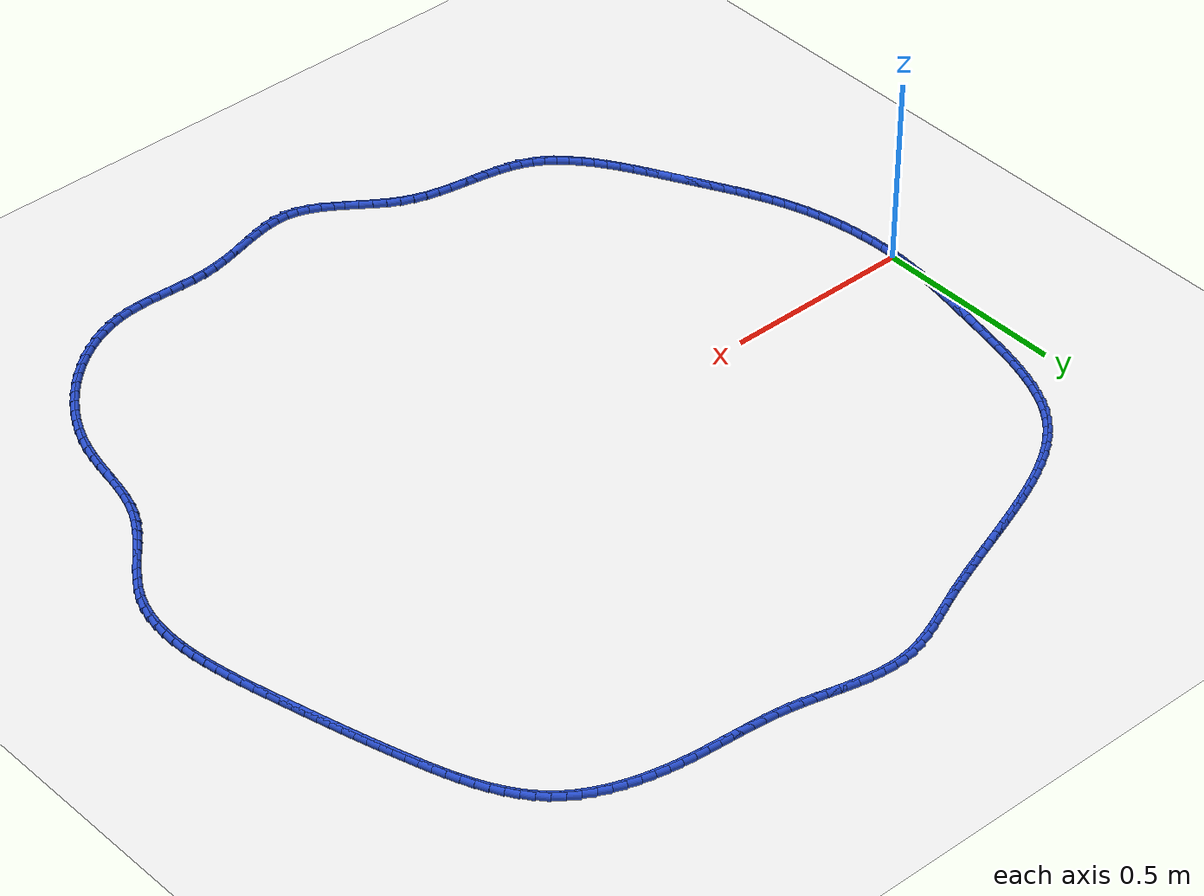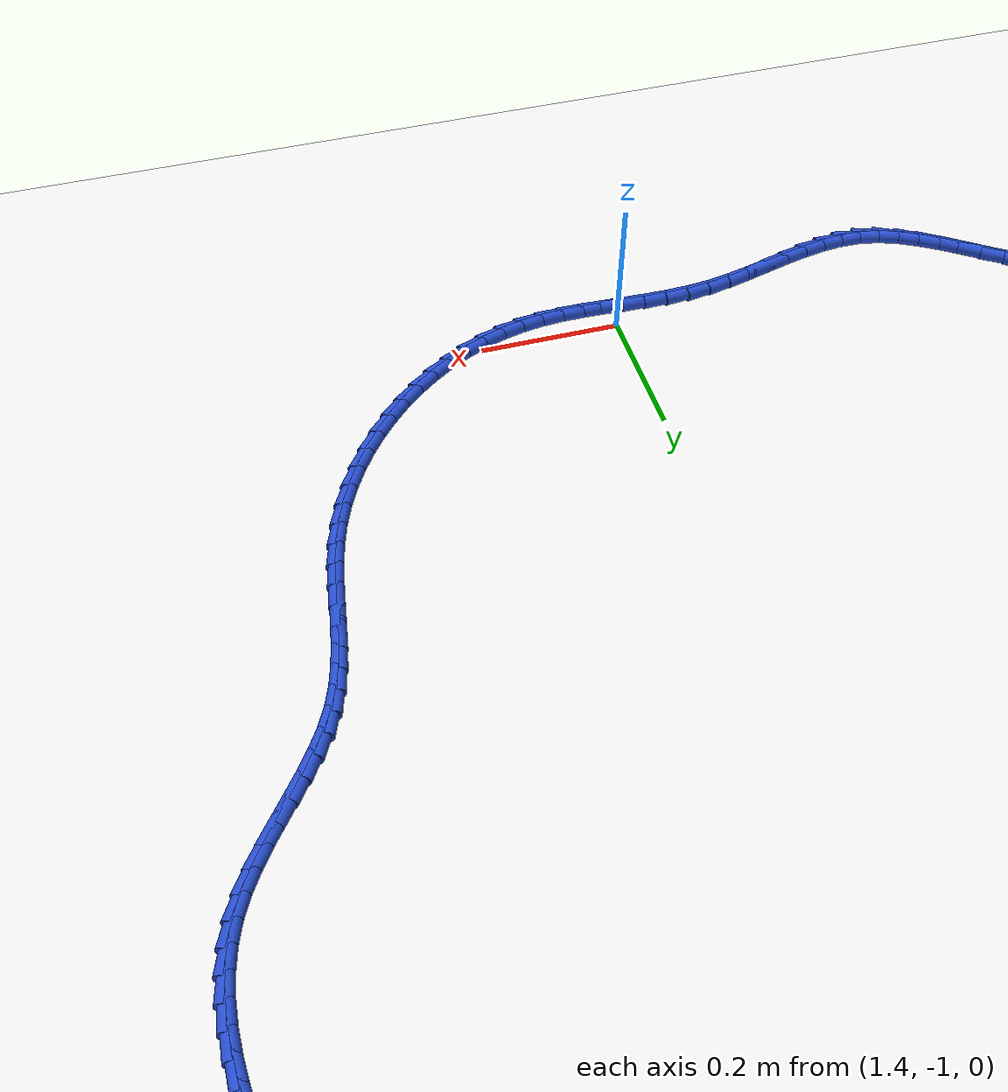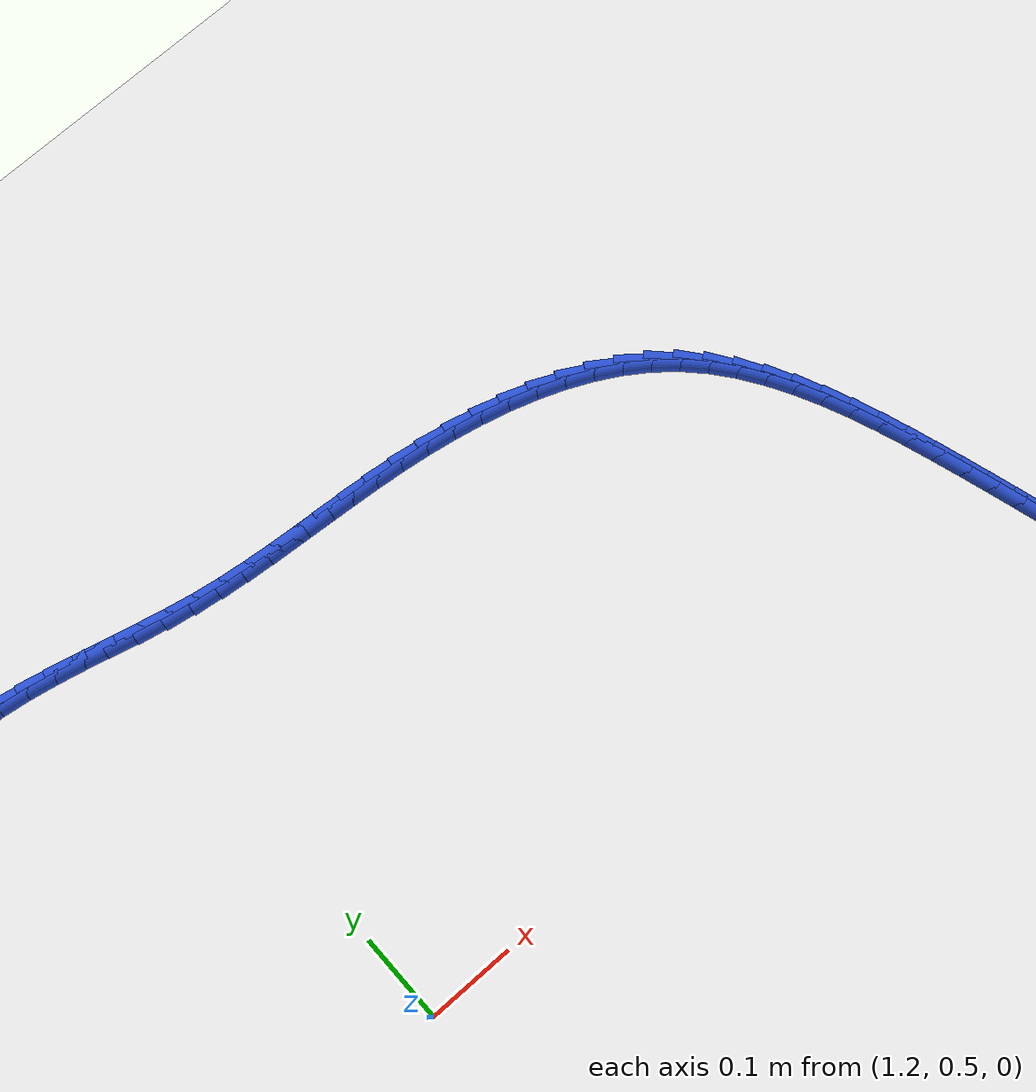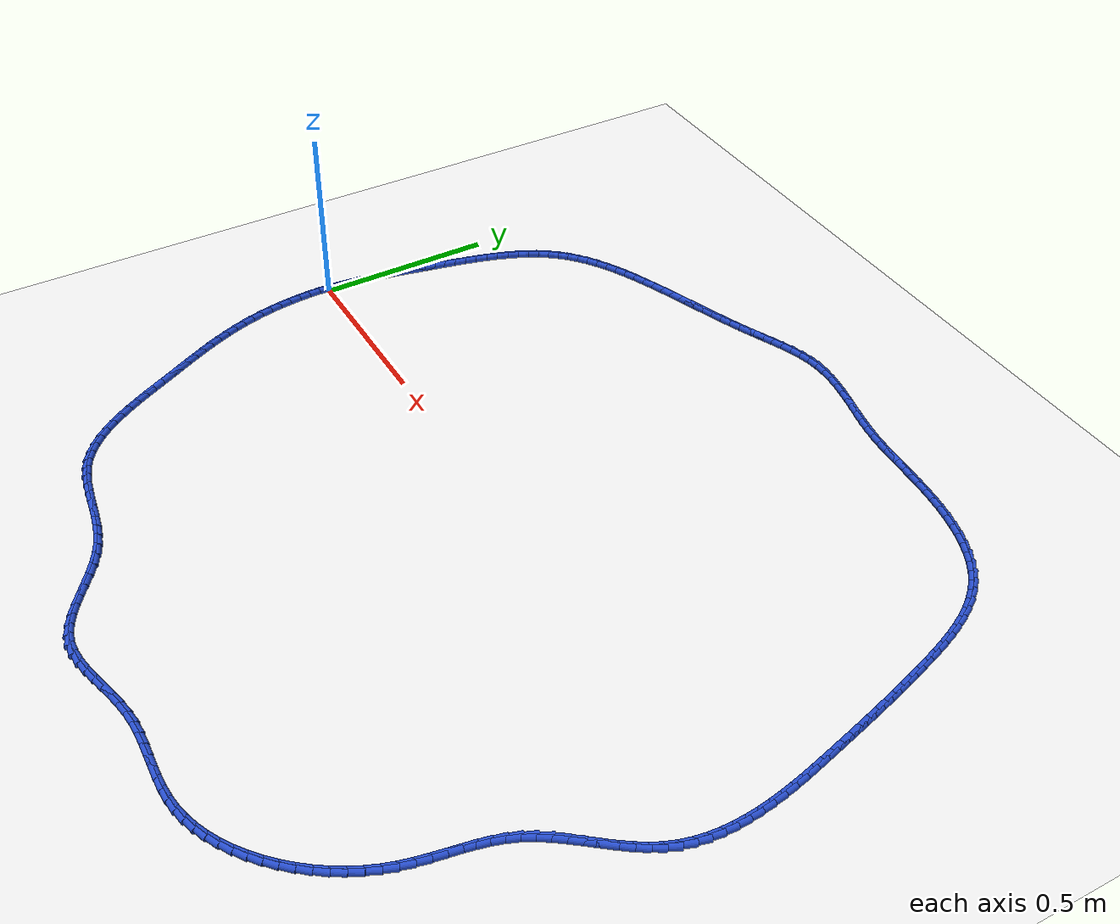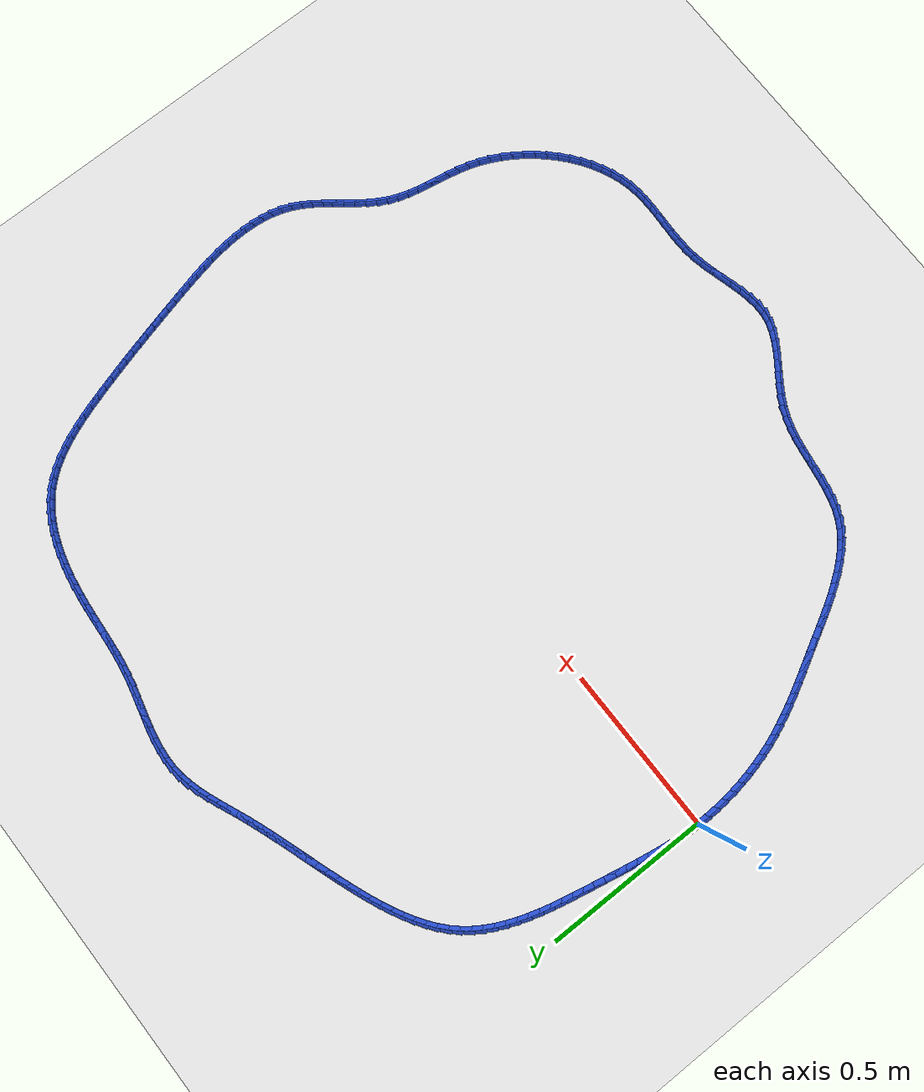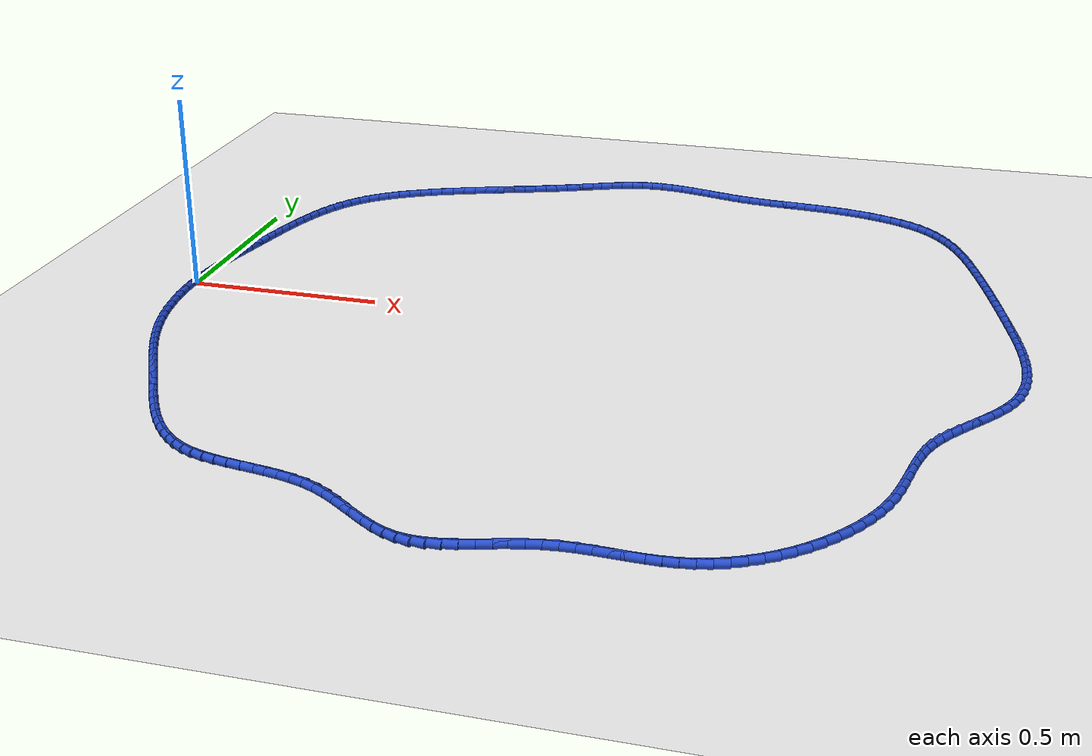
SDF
<sdf version="1.6">
 <world name="default">
  <light name="sun" type="directional">
   <pose>0 0 10 0 -0 0</pose>
   <diffuse>0.8 0.8 0.8 1</diffuse>
   <specular>0.2 0.2 0.2 1</specular>
   <attenuation>
    <range>1000</range>
    <constant>0.9</constant>
    <linear>0.01</linear>
    <quadratic>0.001</quadratic>
   </attenuation>
   <direction>-0.5 0.1 -0.9</direction>
  </light>
  <model name="ground_plane">
   <static>1</static>
   <link name="link">
    <collision name="collision">
     <geometry><plane><normal>0 0 1</normal><size>100 100</size></plane></geometry>
     <surface><friction><ode><mu>100</mu><mu2>50</mu2></ode></friction></surface>
    </collision>
    <visual name="visual">
     <cast_shadows>0</cast_shadows>
     <geometry><plane><normal>0 0 1</normal><size>100 100</size></plane></geometry>
     <material>
      <script><uri>file://media/materials/scripts/gazebo.material</uri><name>Gazebo/WhiteGlow</name></script>
     </material>
    </visual>
   </link>
  </model>
  <gravity>0 0 -9.8</gravity>
  <magnetic_field>6e-06 2.3e-05 -4.2e-05</magnetic_field>
  <atmosphere type="adiabatic"/>
  <physics name="default_physics" default="0" type="ode">
   <max_step_size>0.001</max_step_size>
   <real_time_factor>1</real_time_factor>
   <real_time_update_rate>1000</real_time_update_rate>
  </physics>
  <scene><ambient>0.4 0.4 0.4 1</ambient><background>0.7 0.7 0.7 1</background><shadows>1</shadows></scene>
  <spherical_coordinates>
   <surface_model>EARTH_WGS84</surface_model>
   <latitude_deg>0</latitude_deg>
   <longitude_deg>0</longitude_deg>
   <elevation>0</elevation>
   <heading_deg>0</heading_deg>
  </spherical_coordinates>
  <model name="line">
   <link name="link_0">
    <pose>1.214306433183765e-17 6.938893903907228e-18 0.01 0 1.57 1.5225617370868163</pose>
    <collision name="collision">
     <geometry><cylinder><radius>0.01</radius><length>0.08</length></cylinder></geometry>
    </collision>
    <visual name="visual">
     <material>
      <script><name>Gazebo/Blue</name><uri>file://media/materials/scripts/gazebo.material</uri></script>
     </material>
     <geometry><cylinder><radius>0.01</radius><length>0.08</length></cylinder></geometry>
    </visual>
   </link>
   <link name="link_1">
    <pose>0.001538935067202059 0.03188047018547949 0.01 0 1.57 1.4866853946187928</pose>
    <collision name="collision">
     <geometry><cylinder><radius>0.01</radius><length>0.08</length></cylinder></geometry>
    </collision>
    <visual name="visual">
     <material>
      <script><name>Gazebo/Blue</name><uri>file://media/materials/scripts/gazebo.material</uri></script>
     </material>
     <geometry><cylinder><radius>0.01</radius><length>0.08</length></cylinder></geometry>
    </visual>
   </link>
   <link name="link_2">
    <pose>0.004210966931550192 0.06357346885209629 0.01 0 1.57 1.455333848812436</pose>
    <collision name="collision">
     <geometry><cylinder><radius>0.01</radius><length>0.08</length></cylinder></geometry>
    </collision>
    <visual name="visual">
     <material>
      <script><name>Gazebo/Blue</name><uri>file://media/materials/scripts/gazebo.material</uri></script>
     </material>
     <geometry><cylinder><radius>0.01</radius><length>0.08</length></cylinder></geometry>
    </visual>
   </link>
   <link name="link_3">
    <pose>0.007872541864150538 0.09514466830303787 0.01 0 1.57 1.4287310129041615</pose>
    <collision name="collision">
     <geometry><cylinder><radius>0.01</radius><length>0.08</length></cylinder></geometry>
    </collision>
    <visual name="visual">
     <material>
      <script><name>Gazebo/Blue</name><uri>file://media/materials/scripts/gazebo.material</uri></script>
     </material>
     <geometry><cylinder><radius>0.01</radius><length>0.08</length></cylinder></geometry>
    </visual>
   </link>
   <link name="link_4">
    <pose>0.012380106136109228 0.12665974084149179 0.01 0 1.57 1.4070091517079606</pose>
    <collision name="collision">
     <geometry><cylinder><radius>0.01</radius><length>0.08</length></cylinder></geometry>
    </collision>
    <visual name="visual">
     <material>
      <script><name>Gazebo/Blue</name><uri>file://media/materials/scripts/gazebo.material</uri></script>
     </material>
     <geometry><cylinder><radius>0.01</radius><length>0.08</length></cylinder></geometry>
    </visual>
   </link>
   <link name="link_5">
    <pose>0.017590106018532385 0.15818435877064543 0.01 0 1.57 1.3902243578277642</pose>
    <collision name="collision">
     <geometry><cylinder><radius>0.01</radius><length>0.08</length></cylinder></geometry>
    </collision>
    <visual name="visual">
     <material>
      <script><name>Gazebo/Blue</name><uri>file://media/materials/scripts/gazebo.material</uri></script>
     </material>
     <geometry><cylinder><radius>0.01</radius><length>0.08</length></cylinder></geometry>
    </visual>
   </link>
   <link name="link_6">
    <pose>0.023358987782526146 0.1897841943936864 0.01 0 1.57 1.378371838764414</pose>
    <collision name="collision">
     <geometry><cylinder><radius>0.01</radius><length>0.08</length></cylinder></geometry>
    </collision>
    <visual name="visual">
     <material>
      <script><name>Gazebo/Blue</name><uri>file://media/materials/scripts/gazebo.material</uri></script>
     </material>
     <geometry><cylinder><radius>0.01</radius><length>0.08</length></cylinder></geometry>
    </visual>
   </link>
   <link name="link_7">
    <pose>0.02954319769919665 0.22152492001380222 0.01 0 1.57 1.3713992717515353</pose>
    <collision name="collision">
     <geometry><cylinder><radius>0.01</radius><length>0.08</length></cylinder></geometry>
    </collision>
    <visual name="visual">
     <material>
      <script><name>Gazebo/Blue</name><uri>file://media/materials/scripts/gazebo.material</uri></script>
     </material>
     <geometry><cylinder><radius>0.01</radius><length>0.08</length></cylinder></geometry>
    </visual>
   </link>
   <link name="link_8">
    <pose>0.03599918203964998 0.2534722079341802 0.01 0 1.57 1.36921725694863</pose>
    <collision name="collision">
     <geometry><cylinder><radius>0.01</radius><length>0.08</length></cylinder></geometry>
    </collision>
    <visual name="visual">
     <material>
      <script><name>Gazebo/Blue</name><uri>file://media/materials/scripts/gazebo.material</uri></script>
     </material>
     <geometry><cylinder><radius>0.01</radius><length>0.08</length></cylinder></geometry>
    </visual>
   </link>
   <link name="link_9">
    <pose>0.04258338707499231 0.285691730458008 0.01 0 1.57 1.3710342729951255</pose>
    <collision name="collision">
     <geometry><cylinder><radius>0.01</radius><length>0.08</length></cylinder></geometry>
    </collision>
    <visual name="visual">
     <material>
      <script><name>Gazebo/Blue</name><uri>file://media/materials/scripts/gazebo.material</uri></script>
     </material>
     <geometry><cylinder><radius>0.01</radius><length>0.08</length></cylinder></geometry>
    </visual>
   </link>
   <link name="link_10">
    <pose>0.04917210961871936 0.3182346867112502 0.01 0 1.57 1.370329673234076</pose>
    <collision name="collision">
     <geometry><cylinder><radius>0.01</radius><length>0.08</length></cylinder></geometry>
    </collision>
    <visual name="visual">
     <material>
      <script><name>Gazebo/Blue</name><uri>file://media/materials/scripts/gazebo.material</uri></script>
     </material>
     <geometry><cylinder><radius>0.01</radius><length>0.08</length></cylinder></geometry>
    </visual>
   </link>
   <link name="link_11">
    <pose>0.05583254689926626 0.3510130889159019 0.01 0 1.57 1.3635773732517178</pose>
    <collision name="collision">
     <geometry><cylinder><radius>0.01</radius><length>0.08</length></cylinder></geometry>
    </collision>
    <visual name="visual">
     <material>
      <script><name>Gazebo/Blue</name><uri>file://media/materials/scripts/gazebo.material</uri></script>
     </material>
     <geometry><cylinder><radius>0.01</radius><length>0.08</length></cylinder></geometry>
    </visual>
   </link>
   <link name="link_12">
    <pose>0.06273844161529021 0.38386126620386646 0.01 0 1.57 1.3507266355099148</pose>
    <collision name="collision">
     <geometry><cylinder><radius>0.01</radius><length>0.08</length></cylinder></geometry>
    </collision>
    <visual name="visual">
     <material>
      <script><name>Gazebo/Blue</name><uri>file://media/materials/scripts/gazebo.material</uri></script>
     </material>
     <geometry><cylinder><radius>0.01</radius><length>0.08</length></cylinder></geometry>
    </visual>
   </link>
   <link name="link_13">
    <pose>0.0700646955437524 0.4166127026144865 0.01 0 1.57 1.3316353631254956</pose>
    <collision name="collision">
     <geometry><cylinder><radius>0.01</radius><length>0.08</length></cylinder></geometry>
    </collision>
    <visual name="visual">
     <material>
      <script><name>Gazebo/Blue</name><uri>file://media/materials/scripts/gazebo.material</uri></script>
     </material>
     <geometry><cylinder><radius>0.01</radius><length>0.08</length></cylinder></geometry>
    </visual>
   </link>
   <link name="link_14">
    <pose>0.07798621046161396 0.4491008821871044 0.01 0 1.57 1.30604081625387</pose>
    <collision name="collision">
     <geometry><cylinder><radius>0.01</radius><length>0.08</length></cylinder></geometry>
    </collision>
    <visual name="visual">
     <material>
      <script><name>Gazebo/Blue</name><uri>file://media/materials/scripts/gazebo.material</uri></script>
     </material>
     <geometry><cylinder><radius>0.01</radius><length>0.08</length></cylinder></geometry>
    </visual>
   </link>
   <link name="link_15">
    <pose>0.08667788814583602 0.48115928896106275 0.01 0 1.57 1.2735728215244417</pose>
    <collision name="collision">
     <geometry><cylinder><radius>0.01</radius><length>0.08</length></cylinder></geometry>
    </collision>
    <visual name="visual">
     <material>
      <script><name>Gazebo/Blue</name><uri>file://media/materials/scripts/gazebo.material</uri></script>
     </material>
     <geometry><cylinder><radius>0.01</radius><length>0.08</length></cylinder></geometry>
    </visual>
   </link>
   <link name="link_16">
    <pose>0.09631463037337971 0.512621406975704 0.01 0 1.57 1.2337748024901196</pose>
    <collision name="collision">
     <geometry><cylinder><radius>0.01</radius><length>0.08</length></cylinder></geometry>
    </collision>
    <visual name="visual">
     <material>
      <script><name>Gazebo/Blue</name><uri>file://media/materials/scripts/gazebo.material</uri></script>
     </material>
     <geometry><cylinder><radius>0.01</radius><length>0.08</length></cylinder></geometry>
    </visual>
   </link>
   <link name="link_17">
    <pose>0.10707133892120617 0.5433207202703704 0.01 0 1.57 1.1861391492259479</pose>
    <collision name="collision">
     <geometry><cylinder><radius>0.01</radius><length>0.08</length></cylinder></geometry>
    </collision>
    <visual name="visual">
     <material>
      <script><name>Gazebo/Blue</name><uri>file://media/materials/scripts/gazebo.material</uri></script>
     </material>
     <geometry><cylinder><radius>0.01</radius><length>0.08</length></cylinder></geometry>
    </visual>
   </link>
   <link name="link_18">
    <pose>0.1191229155662766 0.5730907128844047 0.01 0 1.57 1.1301652648463916</pose>
    <collision name="collision">
     <geometry><cylinder><radius>0.01</radius><length>0.08</length></cylinder></geometry>
    </collision>
    <visual name="visual">
     <material>
      <script><name>Gazebo/Blue</name><uri>file://media/materials/scripts/gazebo.material</uri></script>
     </material>
     <geometry><cylinder><radius>0.01</radius><length>0.08</length></cylinder></geometry>
    </visual>
   </link>
   <link name="link_19">
    <pose>0.13264426208555213 0.6017648688571493 0.01 0 1.57 1.065449106538437</pose>
    <collision name="collision">
     <geometry><cylinder><radius>0.01</radius><length>0.08</length></cylinder></geometry>
    </collision>
    <visual name="visual">
     <material>
      <script><name>Gazebo/Blue</name><uri>file://media/materials/scripts/gazebo.material</uri></script>
     </material>
     <geometry><cylinder><radius>0.01</radius><length>0.08</length></cylinder></geometry>
    </visual>
   </link>
   <link name="link_20">
    <pose>0.14781028025599385 0.6291766722279466 0.01 0 1.57 0.991809695278978</pose>
    <collision name="collision">
     <geometry><cylinder><radius>0.01</radius><length>0.08</length></cylinder></geometry>
    </collision>
    <visual name="visual">
     <material>
      <script><name>Gazebo/Blue</name><uri>file://media/materials/scripts/gazebo.material</uri></script>
     </material>
     <geometry><cylinder><radius>0.01</radius><length>0.08</length></cylinder></geometry>
    </visual>
   </link>
   <link name="link_21">
    <pose>0.1647958718545629 0.6551596070361391 0.01 0 1.57 0.9094473548559179</pose>
    <collision name="collision">
     <geometry><cylinder><radius>0.01</radius><length>0.08</length></cylinder></geometry>
    </collision>
    <visual name="visual">
     <material>
      <script><name>Gazebo/Blue</name><uri>file://media/materials/scripts/gazebo.material</uri></script>
     </material>
     <geometry><cylinder><radius>0.01</radius><length>0.08</length></cylinder></geometry>
    </visual>
   </link>
   <link name="link_22">
    <pose>0.1837759386582205 0.6795471573210692 0.01 0 1.57 0.8205057366804371</pose>
    <collision name="collision">
     <geometry><cylinder><radius>0.01</radius><length>0.08</length></cylinder></geometry>
    </collision>
    <visual name="visual">
     <material>
      <script><name>Gazebo/Blue</name><uri>file://media/materials/scripts/gazebo.material</uri></script>
     </material>
     <geometry><cylinder><radius>0.01</radius><length>0.08</length></cylinder></geometry>
    </visual>
   </link>
   <link name="link_23">
    <pose>0.2048900490887264 0.7021983944753233 0.01 0 1.57 0.7361860833241909</pose>
    <collision name="collision">
     <geometry><cylinder><radius>0.01</radius><length>0.08</length></cylinder></geometry>
    </collision>
    <visual name="visual">
     <material>
      <script><name>Gazebo/Blue</name><uri>file://media/materials/scripts/gazebo.material</uri></script>
     </material>
     <geometry><cylinder><radius>0.01</radius><length>0.08</length></cylinder></geometry>
    </visual>
   </link>
   <link name="link_24">
    <pose>0.22802132071984266 0.7231581038832696 0.01 0 1.57 0.6613907636054641</pose>
    <collision name="collision">
     <geometry><cylinder><radius>0.01</radius><length>0.08</length></cylinder></geometry>
    </collision>
    <visual name="visual">
     <material>
      <script><name>Gazebo/Blue</name><uri>file://media/materials/scripts/gazebo.material</uri></script>
     </material>
     <geometry><cylinder><radius>0.01</radius><length>0.08</length></cylinder></geometry>
    </visual>
   </link>
   <link name="link_25">
    <pose>0.25293973699146355 0.7425529992666985 0.01 0 1.57 0.5959907343727335</pose>
    <collision name="collision">
     <geometry><cylinder><radius>0.01</radius><length>0.08</length></cylinder></geometry>
    </collision>
    <visual name="visual">
     <material>
      <script><name>Gazebo/Blue</name><uri>file://media/materials/scripts/gazebo.material</uri></script>
     </material>
     <geometry><cylinder><radius>0.01</radius><length>0.08</length></cylinder></geometry>
    </visual>
   </link>
   <link name="link_26">
    <pose>0.27941478531019587 0.7605101535597917 0.01 0 1.57 0.539514092258927</pose>
    <collision name="collision">
     <geometry><cylinder><radius>0.01</radius><length>0.08</length></cylinder></geometry>
    </collision>
    <visual name="visual">
     <material>
      <script><name>Gazebo/Blue</name><uri>file://media/materials/scripts/gazebo.material</uri></script>
     </material>
     <geometry><cylinder><radius>0.01</radius><length>0.08</length></cylinder></geometry>
    </visual>
   </link>
   <link name="link_27">
    <pose>0.3072159530826459 0.7771566396967292 0.01 0 1.57 0.4913378514632935</pose>
    <collision name="collision">
     <geometry><cylinder><radius>0.01</radius><length>0.08</length></cylinder></geometry>
    </collision>
    <visual name="visual">
     <material>
      <script><name>Gazebo/Blue</name><uri>file://media/materials/scripts/gazebo.material</uri></script>
     </material>
     <geometry><cylinder><radius>0.01</radius><length>0.08</length></cylinder></geometry>
    </visual>
   </link>
   <link name="link_28">
    <pose>0.33611272771542017 0.7926195306116915 0.01 0 1.57 0.4508100851412401</pose>
    <collision name="collision">
     <geometry><cylinder><radius>0.01</radius><length>0.08</length></cylinder></geometry>
    </collision>
    <visual name="visual">
     <material>
      <script><name>Gazebo/Blue</name><uri>file://media/materials/scripts/gazebo.material</uri></script>
     </material>
     <geometry><cylinder><radius>0.01</radius><length>0.08</length></cylinder></geometry>
    </visual>
   </link>
   <link name="link_29">
    <pose>0.3658745966151252 0.80702589923886 0.01 0 1.57 0.4173279921610457</pose>
    <collision name="collision">
     <geometry><cylinder><radius>0.01</radius><length>0.08</length></cylinder></geometry>
    </collision>
    <visual name="visual">
     <material>
      <script><name>Gazebo/Blue</name><uri>file://media/materials/scripts/gazebo.material</uri></script>
     </material>
     <geometry><cylinder><radius>0.01</radius><length>0.08</length></cylinder></geometry>
    </visual>
   </link>
   <link name="link_30">
    <pose>0.39627104718836764 0.820502818512415 0.01 0 1.57 0.3903842734429037</pose>
    <collision name="collision">
     <geometry><cylinder><radius>0.01</radius><length>0.08</length></cylinder></geometry>
    </collision>
    <visual name="visual">
     <material>
      <script><name>Gazebo/Blue</name><uri>file://media/materials/scripts/gazebo.material</uri></script>
     </material>
     <geometry><cylinder><radius>0.01</radius><length>0.08</length></cylinder></geometry>
    </visual>
   </link>
   <link name="link_31">
    <pose>0.4270715668417537 0.8331773613665373 0.01 0 1.57 0.36959403629268767</pose>
    <collision name="collision">
     <geometry><cylinder><radius>0.01</radius><length>0.08</length></cylinder></geometry>
    </collision>
    <visual name="visual">
     <material>
      <script><name>Gazebo/Blue</name><uri>file://media/materials/scripts/gazebo.material</uri></script>
     </material>
     <geometry><cylinder><radius>0.01</radius><length>0.08</length></cylinder></geometry>
    </visual>
   </link>
   <link name="link_32">
    <pose>0.4580456429818903 0.845176600735408 0.01 0 1.57 0.35470477418256385</pose>
    <collision name="collision">
     <geometry><cylinder><radius>0.01</radius><length>0.08</length></cylinder></geometry>
    </collision>
    <visual name="visual">
     <material>
      <script><name>Gazebo/Blue</name><uri>file://media/materials/scripts/gazebo.material</uri></script>
     </material>
     <geometry><cylinder><radius>0.01</radius><length>0.08</length></cylinder></geometry>
    </visual>
   </link>
   <link name="link_33">
    <pose>0.4889633488913533 0.8566275720607001 0.01 0 1.57 0.34464761237326624</pose>
    <collision name="collision">
     <geometry><cylinder><radius>0.01</radius><length>0.08</length></cylinder></geometry>
    </collision>
    <visual name="visual">
     <material>
      <script><name>Gazebo/Blue</name><uri>file://media/materials/scripts/gazebo.material</uri></script>
     </material>
     <geometry><cylinder><radius>0.01</radius><length>0.08</length></cylinder></geometry>
    </visual>
   </link>
   <link name="link_34">
    <pose>0.5196747592132541 0.8676521911824002 0.01 0 1.57 0.3375330570751018</pose>
    <collision name="collision">
     <geometry><cylinder><radius>0.01</radius><length>0.08</length></cylinder></geometry>
    </collision>
    <visual name="visual">
     <material>
      <script><name>Gazebo/Blue</name><uri>file://media/materials/scripts/gazebo.material</uri></script>
     </material>
     <geometry><cylinder><radius>0.01</radius><length>0.08</length></cylinder></geometry>
    </visual>
   </link>
   <link name="link_35">
    <pose>0.5501904814964527 0.8783621008085193 0.01 0 1.57 0.3332415292095401</pose>
    <collision name="collision">
     <geometry><cylinder><radius>0.01</radius><length>0.08</length></cylinder></geometry>
    </collision>
    <visual name="visual">
     <material>
      <script><name>Gazebo/Blue</name><uri>file://media/materials/scripts/gazebo.material</uri></script>
     </material>
     <geometry><cylinder><radius>0.01</radius><length>0.08</length></cylinder></geometry>
    </visual>
   </link>
   <link name="link_36">
    <pose>0.5805403084050387 0.888867715916094 0.01 0 1.57 0.3318586030347969</pose>
    <collision name="collision">
     <geometry><cylinder><radius>0.01</radius><length>0.08</length></cylinder></geometry>
    </collision>
    <visual name="visual">
     <material>
      <script><name>Gazebo/Blue</name><uri>file://media/materials/scripts/gazebo.material</uri></script>
     </material>
     <geometry><cylinder><radius>0.01</radius><length>0.08</length></cylinder></geometry>
    </visual>
   </link>
   <link name="link_37">
    <pose>0.6107540326031021 0.8992794514821613 0.01 0 1.57 0.333436303861949</pose>
    <collision name="collision">
     <geometry><cylinder><radius>0.01</radius><length>0.08</length></cylinder></geometry>
    </collision>
    <visual name="visual">
     <material>
      <script><name>Gazebo/Blue</name><uri>file://media/materials/scripts/gazebo.material</uri></script>
     </material>
     <geometry><cylinder><radius>0.01</radius><length>0.08</length></cylinder></geometry>
    </visual>
   </link>
   <link name="link_38">
    <pose>0.6408614467547329 0.9097077224837575 0.01 0 1.57 0.33799156435182326</pose>
    <collision name="collision">
     <geometry><cylinder><radius>0.01</radius><length>0.08</length></cylinder></geometry>
    </collision>
    <visual name="visual">
     <material>
      <script><name>Gazebo/Blue</name><uri>file://media/materials/scripts/gazebo.material</uri></script>
     </material>
     <geometry><cylinder><radius>0.01</radius><length>0.08</length></cylinder></geometry>
    </visual>
   </link>
   <link name="link_39">
    <pose>0.6708923435240208 0.9202629438979198 0.01 0 1.57 0.3455049410848417</pose>
    <collision name="collision">
     <geometry><cylinder><radius>0.01</radius><length>0.08</length></cylinder></geometry>
    </collision>
    <visual name="visual">
     <material>
      <script><name>Gazebo/Blue</name><uri>file://media/materials/scripts/gazebo.material</uri></script>
     </material>
     <geometry><cylinder><radius>0.01</radius><length>0.08</length></cylinder></geometry>
    </visual>
   </link>
   <link name="link_40">
    <pose>0.700876515575056 0.9310555307016847 0.01 0 1.57 0.35591965508869167</pose>
    <collision name="collision">
     <geometry><cylinder><radius>0.01</radius><length>0.08</length></cylinder></geometry>
    </collision>
    <visual name="visual">
     <material>
      <script><name>Gazebo/Blue</name><uri>file://media/materials/scripts/gazebo.material</uri></script>
     </material>
     <geometry><cylinder><radius>0.01</radius><length>0.08</length></cylinder></geometry>
    </visual>
   </link>
   <link name="link_41">
    <pose>0.7308437555719284 0.942195897872089 0.01 0 1.57 0.3691410917789792</pose>
    <collision name="collision">
     <geometry><cylinder><radius>0.01</radius><length>0.08</length></cylinder></geometry>
    </collision>
    <visual name="visual">
     <material>
      <script><name>Gazebo/Blue</name><uri>file://media/materials/scripts/gazebo.material</uri></script>
     </material>
     <geometry><cylinder><radius>0.01</radius><length>0.08</length></cylinder></geometry>
    </visual>
   </link>
   <link name="link_42">
    <pose>0.7608238561787277 0.9537944603861697 0.01 0 1.57 0.3850367574353418</pose>
    <collision name="collision">
     <geometry><cylinder><radius>0.01</radius><length>0.08</length></cylinder></geometry>
    </collision>
    <visual name="visual">
     <material>
      <script><name>Gazebo/Blue</name><uri>file://media/materials/scripts/gazebo.material</uri></script>
     </material>
     <geometry><cylinder><radius>0.01</radius><length>0.08</length></cylinder></geometry>
    </visual>
   </link>
   <link name="link_43">
    <pose>0.790846610019837 0.9659616262527786 0.01 0 1.57 0.399595309721922</pose>
    <collision name="collision">
     <geometry><cylinder><radius>0.01</radius><length>0.08</length></cylinder></geometry>
    </collision>
    <visual name="visual">
     <material>
      <script><name>Gazebo/Blue</name><uri>file://media/materials/scripts/gazebo.material</uri></script>
     </material>
     <geometry><cylinder><radius>0.01</radius><length>0.08</length></cylinder></geometry>
    </visual>
   </link>
   <link name="link_44">
    <pose>0.8209410301037435 0.9786709894901663 0.01 0 1.57 0.3992236961994275</pose>
    <collision name="collision">
     <geometry><cylinder><radius>0.01</radius><length>0.08</length></cylinder></geometry>
    </collision>
    <visual name="visual">
     <material>
      <script><name>Gazebo/Blue</name><uri>file://media/materials/scripts/gazebo.material</uri></script>
     </material>
     <geometry><cylinder><radius>0.01</radius><length>0.08</length></cylinder></geometry>
    </visual>
   </link>
   <link name="link_45">
    <pose>0.8511333505443315 0.9914084787642047 0.01 0 1.57 0.3809783282690626</pose>
    <collision name="collision">
     <geometry><cylinder><radius>0.01</radius><length>0.08</length></cylinder></geometry>
    </collision>
    <visual name="visual">
     <material>
      <script><name>Gazebo/Blue</name><uri>file://media/materials/scripts/gazebo.material</uri></script>
     </material>
     <geometry><cylinder><radius>0.01</radius><length>0.08</length></cylinder></geometry>
    </visual>
   </link>
   <link name="link_46">
    <pose>0.8814491865583146 1.0035514131136682 0.01 0 1.57 0.3443436118369045</pose>
    <collision name="collision">
     <geometry><cylinder><radius>0.01</radius><length>0.08</length></cylinder></geometry>
    </collision>
    <visual name="visual">
     <material>
      <script><name>Gazebo/Blue</name><uri>file://media/materials/scripts/gazebo.material</uri></script>
     </material>
     <geometry><cylinder><radius>0.01</radius><length>0.08</length></cylinder></geometry>
    </visual>
   </link>
   <link name="link_47">
    <pose>0.9119141533624072 1.0144771115773321 0.01 0 1.57 0.2882759029482726</pose>
    <collision name="collision">
     <geometry><cylinder><radius>0.01</radius><length>0.08</length></cylinder></geometry>
    </collision>
    <visual name="visual">
     <material>
      <script><name>Gazebo/Blue</name><uri>file://media/materials/scripts/gazebo.material</uri></script>
     </material>
     <geometry><cylinder><radius>0.01</radius><length>0.08</length></cylinder></geometry>
    </visual>
   </link>
   <link name="link_48">
    <pose>0.9425538661733233 1.0235628931939709 0.01 0 1.57 0.21154580744749787</pose>
    <collision name="collision">
     <geometry><cylinder><radius>0.01</radius><length>0.08</length></cylinder></geometry>
    </collision>
    <visual name="visual">
     <material>
      <script><name>Gazebo/Blue</name><uri>file://media/materials/scripts/gazebo.material</uri></script>
     </material>
     <geometry><cylinder><radius>0.01</radius><length>0.08</length></cylinder></geometry>
    </visual>
   </link>
   <link name="link_49">
    <pose>0.9733939402077765 1.0301860770023596 0.01 0 1.57 0.11388824594464175</pose>
    <collision name="collision">
     <geometry><cylinder><radius>0.01</radius><length>0.08</length></cylinder></geometry>
    </collision>
    <visual name="visual">
     <material>
      <script><name>Gazebo/Blue</name><uri>file://media/materials/scripts/gazebo.material</uri></script>
     </material>
     <geometry><cylinder><radius>0.01</radius><length>0.08</length></cylinder></geometry>
    </visual>
   </link>
   <link name="link_50">
    <pose>1.004459181032475 1.0337394190032192 0.01 0 1.57 0.011984955771441548</pose>
    <collision name="collision">
     <geometry><cylinder><radius>0.01</radius><length>0.08</length></cylinder></geometry>
    </collision>
    <visual name="visual">
     <material>
      <script><name>Gazebo/Blue</name><uri>file://media/materials/scripts/gazebo.material</uri></script>
     </material>
     <geometry><cylinder><radius>0.01</radius><length>0.08</length></cylinder></geometry>
    </visual>
   </link>
   <link name="link_51">
    <pose>1.0357482348710128 1.0341144348854323 0.01 0 1.57 -0.07347195860439526</pose>
    <collision name="collision">
     <geometry><cylinder><radius>0.01</radius><length>0.08</length></cylinder></geometry>
    </collision>
    <visual name="visual">
     <material>
      <script><name>Gazebo/Blue</name><uri>file://media/materials/scripts/gazebo.material</uri></script>
     </material>
     <geometry><cylinder><radius>0.01</radius><length>0.08</length></cylinder></geometry>
    </visual>
   </link>
   <link name="link_52">
    <pose>1.067228556501514 1.0317973431767844 0.01 0 1.57 -0.14092321967316881</pose>
    <collision name="collision">
     <geometry><cylinder><radius>0.01</radius><length>0.08</length></cylinder></geometry>
    </collision>
    <visual name="visual">
     <material>
      <script><name>Gazebo/Blue</name><uri>file://media/materials/scripts/gazebo.material</uri></script>
     </material>
     <geometry><cylinder><radius>0.01</radius><length>0.08</length></cylinder></geometry>
    </visual>
   </link>
   <link name="link_53">
    <pose>1.0988657748558754 1.027309174383815 0.01 0 1.57 -0.19091640344043287</pose>
    <collision name="collision">
     <geometry><cylinder><radius>0.01</radius><length>0.08</length></cylinder></geometry>
    </collision>
    <visual name="visual">
     <material>
      <script><name>Gazebo/Blue</name><uri>file://media/materials/scripts/gazebo.material</uri></script>
     </material>
     <geometry><cylinder><radius>0.01</radius><length>0.08</length></cylinder></geometry>
    </visual>
   </link>
   <link name="link_54">
    <pose>1.1306255188659904 1.0211709590130635 0.01 0 1.57 -0.22434445367378456</pose>
    <collision name="collision">
     <geometry><cylinder><radius>0.01</radius><length>0.08</length></cylinder></geometry>
    </collision>
    <visual name="visual">
     <material>
      <script><name>Gazebo/Blue</name><uri>file://media/materials/scripts/gazebo.material</uri></script>
     </material>
     <geometry><cylinder><radius>0.01</radius><length>0.08</length></cylinder></geometry>
    </visual>
   </link>
   <link name="link_55">
    <pose>1.1624734174637537 1.0139037275710685 0.01 0 1.57 -0.2420202399970399</pose>
    <collision name="collision">
     <geometry><cylinder><radius>0.01</radius><length>0.08</length></cylinder></geometry>
    </collision>
    <visual name="visual">
     <material>
      <script><name>Gazebo/Blue</name><uri>file://media/materials/scripts/gazebo.material</uri></script>
     </material>
     <geometry><cylinder><radius>0.01</radius><length>0.08</length></cylinder></geometry>
    </visual>
   </link>
   <link name="link_56">
    <pose>1.194375099581061 1.0060285105643703 0.01 0 1.57 -0.24444487658945324</pose>
    <collision name="collision">
     <geometry><cylinder><radius>0.01</radius><length>0.08</length></cylinder></geometry>
    </collision>
    <visual name="visual">
     <material>
      <script><name>Gazebo/Blue</name><uri>file://media/materials/scripts/gazebo.material</uri></script>
     </material>
     <geometry><cylinder><radius>0.01</radius><length>0.08</length></cylinder></geometry>
    </visual>
   </link>
   <link name="link_57">
    <pose>1.2262961941498063 0.9980663384995075 0.01 0 1.57 -0.2317074153687437</pose>
    <collision name="collision">
     <geometry><cylinder><radius>0.01</radius><length>0.08</length></cylinder></geometry>
    </collision>
    <visual name="visual">
     <material>
      <script><name>Gazebo/Blue</name><uri>file://media/materials/scripts/gazebo.material</uri></script>
     </material>
     <geometry><cylinder><radius>0.01</radius><length>0.08</length></cylinder></geometry>
    </visual>
   </link>
   <link name="link_58">
    <pose>1.2582023301018848 0.9905382418830202 0.01 0 1.57 -0.20347389535031427</pose>
    <collision name="collision">
     <geometry><cylinder><radius>0.01</radius><length>0.08</length></cylinder></geometry>
    </collision>
    <visual name="visual">
     <material>
      <script><name>Gazebo/Blue</name><uri>file://media/materials/scripts/gazebo.material</uri></script>
     </material>
     <geometry><cylinder><radius>0.01</radius><length>0.08</length></cylinder></geometry>
    </visual>
   </link>
   <link name="link_59">
    <pose>1.2900591363691911 0.9839652512214471 0.01 0 1.57 -0.16301592677326354</pose>
    <collision name="collision">
     <geometry><cylinder><radius>0.01</radius><length>0.08</length></cylinder></geometry>
    </collision>
    <visual name="visual">
     <material>
      <script><name>Gazebo/Blue</name><uri>file://media/materials/scripts/gazebo.material</uri></script>
     </material>
     <geometry><cylinder><radius>0.01</radius><length>0.08</length></cylinder></geometry>
    </visual>
   </link>
   <link name="link_60">
    <pose>1.3218439203575756 0.9787374346189551 0.01 0 1.57 -0.12669041119045063</pose>
    <collision name="collision">
     <geometry><cylinder><radius>0.01</radius><length>0.08</length></cylinder></geometry>
    </collision>
    <visual name="visual">
     <material>
      <script><name>Gazebo/Blue</name><uri>file://media/materials/scripts/gazebo.material</uri></script>
     </material>
     <geometry><cylinder><radius>0.01</radius><length>0.08</length></cylinder></geometry>
    </visual>
   </link>
   <link name="link_61">
    <pose>1.3535830460704898 0.9746947395133077 0.01 0 1.57 -0.09931853524672662</pose>
    <collision name="collision">
     <geometry><cylinder><radius>0.01</radius><length>0.08</length></cylinder></geometry>
    </collision>
    <visual name="visual">
     <material>
      <script><name>Gazebo/Blue</name><uri>file://media/materials/scripts/gazebo.material</uri></script>
     </material>
     <geometry><cylinder><radius>0.01</radius><length>0.08</length></cylinder></geometry>
    </visual>
   </link>
   <link name="link_62">
    <pose>1.3853157564118472 0.9715326893575623 0.01 0 1.57 -0.08122616724734065</pose>
    <collision name="collision">
     <geometry><cylinder><radius>0.01</radius><length>0.08</length></cylinder></geometry>
    </collision>
    <visual name="visual">
     <material>
      <script><name>Gazebo/Blue</name><uri>file://media/materials/scripts/gazebo.material</uri></script>
     </material>
     <geometry><cylinder><radius>0.01</radius><length>0.08</length></cylinder></geometry>
    </visual>
   </link>
   <link name="link_63">
    <pose>1.4170812943387743 0.9689468070080014 0.01 0 1.57 -0.07255975022171056</pose>
    <collision name="collision">
     <geometry><cylinder><radius>0.01</radius><length>0.08</length></cylinder></geometry>
    </collision>
    <visual name="visual">
     <material>
      <script><name>Gazebo/Blue</name><uri>file://media/materials/scripts/gazebo.material</uri></script>
     </material>
     <geometry><cylinder><radius>0.01</radius><length>0.08</length></cylinder></geometry>
    </visual>
   </link>
   <link name="link_64">
    <pose>1.448918902808399 0.9666326153209082 0.01 0 1.57 -0.07332860959001396</pose>
    <collision name="collision">
     <geometry><cylinder><radius>0.01</radius><length>0.08</length></cylinder></geometry>
    </collision>
    <visual name="visual">
     <material>
      <script><name>Gazebo/Blue</name><uri>file://media/materials/scripts/gazebo.material</uri></script>
     </material>
     <geometry><cylinder><radius>0.01</radius><length>0.08</length></cylinder></geometry>
    </visual>
   </link>
   <link name="link_65">
    <pose>1.4808678247778504 0.9642856371525648 0.01 0 1.57 -0.08342849513916002</pose>
    <collision name="collision">
     <geometry><cylinder><radius>0.01</radius><length>0.08</length></cylinder></geometry>
    </collision>
    <visual name="visual">
     <material>
      <script><name>Gazebo/Blue</name><uri>file://media/materials/scripts/gazebo.material</uri></script>
     </material>
     <geometry><cylinder><radius>0.01</radius><length>0.08</length></cylinder></geometry>
    </visual>
   </link>
   <link name="link_66">
    <pose>1.5129673032042559 0.9616013953592545 0.01 0 1.57 -0.10264378768267576</pose>
    <collision name="collision">
     <geometry><cylinder><radius>0.01</radius><length>0.08</length></cylinder></geometry>
    </collision>
    <visual name="visual">
     <material>
      <script><name>Gazebo/Blue</name><uri>file://media/materials/scripts/gazebo.material</uri></script>
     </material>
     <geometry><cylinder><radius>0.01</radius><length>0.08</length></cylinder></geometry>
    </visual>
   </link>
   <link name="link_67">
    <pose>1.5452565810447425 0.9582754127972594 0.01 0 1.57 -0.13062489858151444</pose>
    <collision name="collision">
     <geometry><cylinder><radius>0.01</radius><length>0.08</length></cylinder></geometry>
    </collision>
    <visual name="visual">
     <material>
      <script><name>Gazebo/Blue</name><uri>file://media/materials/scripts/gazebo.material</uri></script>
     </material>
     <geometry><cylinder><radius>0.01</radius><length>0.08</length></cylinder></geometry>
    </visual>
   </link>
   <link name="link_68">
    <pose>1.5777744539581673 0.9540034439205473 0.01 0 1.57 -0.16591214464404036</pose>
    <collision name="collision">
     <geometry><cylinder><radius>0.01</radius><length>0.08</length></cylinder></geometry>
    </collision>
    <visual name="visual">
     <material>
      <script><name>Gazebo/Blue</name><uri>file://media/materials/scripts/gazebo.material</uri></script>
     </material>
     <geometry><cylinder><radius>0.01</radius><length>0.08</length></cylinder></geometry>
    </visual>
   </link>
   <link name="link_69">
    <pose>1.6104676269250393 0.9485289249855973 0.01 0 1.57 -0.2063935028493118</pose>
    <collision name="collision">
     <geometry><cylinder><radius>0.01</radius><length>0.08</length></cylinder></geometry>
    </collision>
    <visual name="visual">
     <material>
      <script><name>Gazebo/Blue</name><uri>file://media/materials/scripts/gazebo.material</uri></script>
     </material>
     <geometry><cylinder><radius>0.01</radius><length>0.08</length></cylinder></geometry>
    </visual>
   </link>
   <link name="link_70">
    <pose>1.6430786663684256 0.9417009890963415 0.01 0 1.57 -0.2524663910348437</pose>
    <collision name="collision">
     <geometry><cylinder><radius>0.01</radius><length>0.08</length></cylinder></geometry>
    </collision>
    <visual name="visual">
     <material>
      <script><name>Gazebo/Blue</name><uri>file://media/materials/scripts/gazebo.material</uri></script>
     </material>
     <geometry><cylinder><radius>0.01</radius><length>0.08</length></cylinder></geometry>
    </visual>
   </link>
   <link name="link_71">
    <pose>1.6753227220631297 0.9333829648782509 0.01 0 1.57 -0.3049659807308782</pose>
    <collision name="collision">
     <geometry><cylinder><radius>0.01</radius><length>0.08</length></cylinder></geometry>
    </collision>
    <visual name="visual">
     <material>
      <script><name>Gazebo/Blue</name><uri>file://media/materials/scripts/gazebo.material</uri></script>
     </material>
     <geometry><cylinder><radius>0.01</radius><length>0.08</length></cylinder></geometry>
    </visual>
   </link>
   <link name="link_72">
    <pose>1.7069149437839555 0.9234381809567971 0.01 0 1.57 -0.3648308515365833</pose>
    <collision name="collision">
     <geometry><cylinder><radius>0.01</radius><length>0.08</length></cylinder></geometry>
    </collision>
    <visual name="visual">
     <material>
      <script><name>Gazebo/Blue</name><uri>file://media/materials/scripts/gazebo.material</uri></script>
     </material>
     <geometry><cylinder><radius>0.01</radius><length>0.08</length></cylinder></geometry>
    </visual>
   </link>
   <link name="link_73">
    <pose>1.7375704813057076 0.911729965957451 0.01 0 1.57 -0.43306276915349406</pose>
    <collision name="collision">
     <geometry><cylinder><radius>0.01</radius><length>0.08</length></cylinder></geometry>
    </collision>
    <visual name="visual">
     <material>
      <script><name>Gazebo/Blue</name><uri>file://media/materials/scripts/gazebo.material</uri></script>
     </material>
     <geometry><cylinder><radius>0.01</radius><length>0.08</length></cylinder></geometry>
    </visual>
   </link>
   <link name="link_74">
    <pose>1.7670044844031894 0.898121648505685 0.01 0 1.57 -0.5106416367463223</pose>
    <collision name="collision">
     <geometry><cylinder><radius>0.01</radius><length>0.08</length></cylinder></geometry>
    </collision>
    <visual name="visual">
     <material>
      <script><name>Gazebo/Blue</name><uri>file://media/materials/scripts/gazebo.material</uri></script>
     </material>
     <geometry><cylinder><radius>0.01</radius><length>0.08</length></cylinder></geometry>
    </visual>
   </link>
   <link name="link_75">
    <pose>1.7949321028512037 0.8824765572269694 0.01 0 1.57 -0.5983738358917429</pose>
    <collision name="collision">
     <geometry><cylinder><radius>0.01</radius><length>0.08</length></cylinder></geometry>
    </collision>
    <visual name="visual">
     <material>
      <script><name>Gazebo/Blue</name><uri>file://media/materials/scripts/gazebo.material</uri></script>
     </material>
     <geometry><cylinder><radius>0.01</radius><length>0.08</length></cylinder></geometry>
    </visual>
   </link>
   <link name="link_76">
    <pose>1.8210684864245552 0.8646580207467754 0.01 0 1.57 -0.6966565141751326</pose>
    <collision name="collision">
     <geometry><cylinder><radius>0.01</radius><length>0.08</length></cylinder></geometry>
    </collision>
    <visual name="visual">
     <material>
      <script><name>Gazebo/Blue</name><uri>file://media/materials/scripts/gazebo.material</uri></script>
     </material>
     <geometry><cylinder><radius>0.01</radius><length>0.08</length></cylinder></geometry>
    </visual>
   </link>
   <link name="link_77">
    <pose>1.8451288285941922 0.8445294058192063 0.01 0 1.57 -0.800853707199921</pose>
    <collision name="collision">
     <geometry><cylinder><radius>0.01</radius><length>0.08</length></cylinder></geometry>
    </collision>
    <visual name="visual">
     <material>
      <script><name>Gazebo/Blue</name><uri>file://media/materials/scripts/gazebo.material</uri></script>
     </material>
     <geometry><cylinder><radius>0.01</radius><length>0.08</length></cylinder></geometry>
    </visual>
   </link>
   <link name="link_78">
    <pose>1.8669304731799221 0.8220432141323843 0.01 0 1.57 -0.896264361814733</pose>
    <collision name="collision">
     <geometry><cylinder><radius>0.01</radius><length>0.08</length></cylinder></geometry>
    </collision>
    <visual name="visual">
     <material>
      <script><name>Gazebo/Blue</name><uri>file://media/materials/scripts/gazebo.material</uri></script>
     </material>
     <geometry><cylinder><radius>0.01</radius><length>0.08</length></cylinder></geometry>
    </visual>
   </link>
   <link name="link_79">
    <pose>1.8866112982026828 0.7974316409358165 0.01 0 1.57 -0.9794710617785285</pose>
    <collision name="collision">
     <geometry><cylinder><radius>0.01</radius><length>0.08</length></cylinder></geometry>
    </collision>
    <visual name="visual">
     <material>
      <script><name>Gazebo/Blue</name><uri>file://media/materials/scripts/gazebo.material</uri></script>
     </material>
     <geometry><cylinder><radius>0.01</radius><length>0.08</length></cylinder></geometry>
    </visual>
   </link>
   <link name="link_80">
    <pose>1.9043718871836628 0.77098159740206 0.01 0 1.57 -1.0505734589829416</pose>
    <collision name="collision">
     <geometry><cylinder><radius>0.01</radius><length>0.08</length></cylinder></geometry>
    </collision>
    <visual name="visual">
     <material>
      <script><name>Gazebo/Blue</name><uri>file://media/materials/scripts/gazebo.material</uri></script>
     </material>
     <geometry><cylinder><radius>0.01</radius><length>0.08</length></cylinder></geometry>
    </visual>
   </link>
   <link name="link_81">
    <pose>1.9204128236440527 0.7429799947036715 0.01 0 1.57 -1.1101946010710217</pose>
    <collision name="collision">
     <geometry><cylinder><radius>0.01</radius><length>0.08</length></cylinder></geometry>
    </collision>
    <visual name="visual">
     <material>
      <script><name>Gazebo/Blue</name><uri>file://media/materials/scripts/gazebo.material</uri></script>
     </material>
     <geometry><cylinder><radius>0.01</radius><length>0.08</length></cylinder></geometry>
    </visual>
   </link>
   <link name="link_82">
    <pose>1.9349346911050418 0.7137137440132076 0.01 0 1.57 -1.1591732860625918</pose>
    <collision name="collision">
     <geometry><cylinder><radius>0.01</radius><length>0.08</length></cylinder></geometry>
    </collision>
    <visual name="visual">
     <material>
      <script><name>Gazebo/Blue</name><uri>file://media/materials/scripts/gazebo.material</uri></script>
     </material>
     <geometry><cylinder><radius>0.01</radius><length>0.08</length></cylinder></geometry>
    </visual>
   </link>
   <link name="link_83">
    <pose>1.9481380730878202 0.6834697565032264 0.01 0 1.57 -1.1983538861379925</pose>
    <collision name="collision">
     <geometry><cylinder><radius>0.01</radius><length>0.08</length></cylinder></geometry>
    </collision>
    <visual name="visual">
     <material>
      <script><name>Gazebo/Blue</name><uri>file://media/materials/scripts/gazebo.material</uri></script>
     </material>
     <geometry><cylinder><radius>0.01</radius><length>0.08</length></cylinder></geometry>
    </visual>
   </link>
   <link name="link_84">
    <pose>1.9602235531135768 0.6525349433462837 0.01 0 1.57 -1.2284585722076924</pose>
    <collision name="collision">
     <geometry><cylinder><radius>0.01</radius><length>0.08</length></cylinder></geometry>
    </collision>
    <visual name="visual">
     <material>
      <script><name>Gazebo/Blue</name><uri>file://media/materials/scripts/gazebo.material</uri></script>
     </material>
     <geometry><cylinder><radius>0.01</radius><length>0.08</length></cylinder></geometry>
    </visual>
   </link>
   <link name="link_85">
    <pose>1.9713917147035023 0.6211962157149366 0.01 0 1.57 -1.2500136431465538</pose>
    <collision name="collision">
     <geometry><cylinder><radius>0.01</radius><length>0.08</length></cylinder></geometry>
    </collision>
    <visual name="visual">
     <material>
      <script><name>Gazebo/Blue</name><uri>file://media/materials/scripts/gazebo.material</uri></script>
     </material>
     <geometry><cylinder><radius>0.01</radius><length>0.08</length></cylinder></geometry>
    </visual>
   </link>
   <link name="link_86">
    <pose>1.9818431413787851 0.5897404847817422 0.01 0 1.57 -1.2633660580823134</pose>
    <collision name="collision">
     <geometry><cylinder><radius>0.01</radius><length>0.08</length></cylinder></geometry>
    </collision>
    <visual name="visual">
     <material>
      <script><name>Gazebo/Blue</name><uri>file://media/materials/scripts/gazebo.material</uri></script>
     </material>
     <geometry><cylinder><radius>0.01</radius><length>0.08</length></cylinder></geometry>
    </visual>
   </link>
   <link name="link_87">
    <pose>1.9917771959486954 0.5584517709949424 0.01 0 1.57 -1.2716342790600534</pose>
    <collision name="collision">
     <geometry><cylinder><radius>0.01</radius><length>0.08</length></cylinder></geometry>
    </collision>
    <visual name="visual">
     <material>
      <script><name>Gazebo/Blue</name><uri>file://media/materials/scripts/gazebo.material</uri></script>
     </material>
     <geometry><cylinder><radius>0.01</radius><length>0.08</length></cylinder></geometry>
    </visual>
   </link>
   <link name="link_88">
    <pose>2.0013324791103844 0.5274702062144678 0.01 0 1.57 -1.2791920324950457</pose>
    <collision name="collision">
     <geometry><cylinder><radius>0.01</radius><length>0.08</length></cylinder></geometry>
    </collision>
    <visual name="visual">
     <material>
      <script><name>Gazebo/Blue</name><uri>file://media/materials/scripts/gazebo.material</uri></script>
     </material>
     <geometry><cylinder><radius>0.01</radius><length>0.08</length></cylinder></geometry>
    </visual>
   </link>
   <link name="link_89">
    <pose>2.010559961263603 0.49672840812165353 0.01 0 1.57 -1.2863081202444147</pose>
    <collision name="collision">
     <geometry><cylinder><radius>0.01</radius><length>0.08</length></cylinder></geometry>
    </collision>
    <visual name="visual">
     <material>
      <script><name>Gazebo/Blue</name><uri>file://media/materials/scripts/gazebo.material</uri></script>
     </material>
     <geometry><cylinder><radius>0.01</radius><length>0.08</length></cylinder></geometry>
    </visual>
   </link>
   <link name="link_90">
    <pose>2.0195037915845955 0.46614284130197825 0.01 0 1.57 -1.2929098659598606</pose>
    <collision name="collision">
     <geometry><cylinder><radius>0.01</radius><length>0.08</length></cylinder></geometry>
    </collision>
    <visual name="visual">
     <material>
      <script><name>Gazebo/Blue</name><uri>file://media/materials/scripts/gazebo.material</uri></script>
     </material>
     <geometry><cylinder><radius>0.01</radius><length>0.08</length></cylinder></geometry>
    </visual>
   </link>
   <link name="link_91">
    <pose>2.0282081192496015 0.4356299703409211 0.01 0 1.57 -1.298932232212982</pose>
    <collision name="collision">
     <geometry><cylinder><radius>0.01</radius><length>0.08</length></cylinder></geometry>
    </collision>
    <visual name="visual">
     <material>
      <script><name>Gazebo/Blue</name><uri>file://media/materials/scripts/gazebo.material</uri></script>
     </material>
     <geometry><cylinder><radius>0.01</radius><length>0.08</length></cylinder></geometry>
    </visual>
   </link>
   <link name="link_92">
    <pose>2.0367170934348646 0.40510625982396126 0.01 0 1.57 -1.3043198552521753</pose>
    <collision name="collision">
     <geometry><cylinder><radius>0.01</radius><length>0.08</length></cylinder></geometry>
    </collision>
    <visual name="visual">
     <material>
      <script><name>Gazebo/Blue</name><uri>file://media/materials/scripts/gazebo.material</uri></script>
     </material>
     <geometry><cylinder><radius>0.01</radius><length>0.08</length></cylinder></geometry>
    </visual>
   </link>
   <link name="link_93">
    <pose>2.0450748633166267 0.3744881743365785 0.01 0 1.57 -1.309028673989975</pose>
    <collision name="collision">
     <geometry><cylinder><radius>0.01</radius><length>0.08</length></cylinder></geometry>
    </collision>
    <visual name="visual">
     <material>
      <script><name>Gazebo/Blue</name><uri>file://media/materials/scripts/gazebo.material</uri></script>
     </material>
     <geometry><cylinder><radius>0.01</radius><length>0.08</length></cylinder></geometry>
    </visual>
   </link>
   <link name="link_94">
    <pose>2.0533255780711293 0.3436921784642519 0.01 0 1.57 -1.313027056629133</pose>
    <collision name="collision">
     <geometry><cylinder><radius>0.01</radius><length>0.08</length></cylinder></geometry>
    </collision>
    <visual name="visual">
     <material>
      <script><name>Gazebo/Blue</name><uri>file://media/materials/scripts/gazebo.material</uri></script>
     </material>
     <geometry><cylinder><radius>0.01</radius><length>0.08</length></cylinder></geometry>
    </visual>
   </link>
   <link name="link_95">
    <pose>2.0615133868746147 0.31263473679246023 0.01 0 1.57 -1.3162963697528909</pose>
    <collision name="collision">
     <geometry><cylinder><radius>0.01</radius><length>0.08</length></cylinder></geometry>
    </collision>
    <visual name="visual">
     <material>
      <script><name>Gazebo/Blue</name><uri>file://media/materials/scripts/gazebo.material</uri></script>
     </material>
     <geometry><cylinder><radius>0.01</radius><length>0.08</length></cylinder></geometry>
    </visual>
   </link>
   <link name="link_96">
    <pose>2.069682438903324 0.28123231390668346 0.01 0 1.57 -1.3188309800878408</pose>
    <collision name="collision">
     <geometry><cylinder><radius>0.01</radius><length>0.08</length></cylinder></geometry>
    </collision>
    <visual name="visual">
     <material>
      <script><name>Gazebo/Blue</name><uri>file://media/materials/scripts/gazebo.material</uri></script>
     </material>
     <geometry><cylinder><radius>0.01</radius><length>0.08</length></cylinder></geometry>
    </visual>
   </link>
   <link name="link_97">
    <pose>2.0778768833335013 0.24940137439240057 0.01 0 1.57 -1.3211867419211731</pose>
    <collision name="collision">
     <geometry><cylinder><radius>0.01</radius><length>0.08</length></cylinder></geometry>
    </collision>
    <visual name="visual">
     <material>
      <script><name>Gazebo/Blue</name><uri>file://media/materials/scripts/gazebo.material</uri></script>
     </material>
     <geometry><cylinder><radius>0.01</radius><length>0.08</length></cylinder></geometry>
    </visual>
   </link>
   <link name="link_98">
    <pose>2.086117661757846 0.2170752270826604 0.01 0 1.57 -1.3274167693040453</pose>
    <collision name="collision">
     <geometry><cylinder><radius>0.01</radius><length>0.08</length></cylinder></geometry>
    </collision>
    <visual name="visual">
     <material>
      <script><name>Gazebo/Blue</name><uri>file://media/materials/scripts/gazebo.material</uri></script>
     </material>
     <geometry><cylinder><radius>0.01</radius><length>0.08</length></cylinder></geometry>
    </visual>
   </link>
   <link name="link_99">
    <pose>2.0942526224229137 0.18431281332929716 0.01 0 1.57 -1.339288706235089</pose>
    <collision name="collision">
     <geometry><cylinder><radius>0.01</radius><length>0.08</length></cylinder></geometry>
    </collision>
    <visual name="visual">
     <material>
      <script><name>Gazebo/Blue</name><uri>file://media/materials/scripts/gazebo.material</uri></script>
     </material>
     <geometry><cylinder><radius>0.01</radius><length>0.08</length></cylinder></geometry>
    </visual>
   </link>
   <link name="link_100">
    <pose>2.102051412087874 0.1512298337418025 0.01 0 1.57 -1.3568660119560731</pose>
    <collision name="collision">
     <geometry><cylinder><radius>0.01</radius><length>0.08</length></cylinder></geometry>
    </collision>
    <visual name="visual">
     <material>
      <script><name>Gazebo/Blue</name><uri>file://media/materials/scripts/gazebo.material</uri></script>
     </material>
     <geometry><cylinder><radius>0.01</radius><length>0.08</length></cylinder></geometry>
    </visual>
   </link>
   <link name="link_101">
    <pose>2.109283295141774 0.11794226645692603 0.01 0 1.57 -1.3803531507674085</pose>
    <collision name="collision">
     <geometry><cylinder><radius>0.01</radius><length>0.08</length></cylinder></geometry>
    </collision>
    <visual name="visual">
     <material>
      <script><name>Gazebo/Blue</name><uri>file://media/materials/scripts/gazebo.material</uri></script>
     </material>
     <geometry><cylinder><radius>0.01</radius><length>0.08</length></cylinder></geometry>
    </visual>
   </link>
   <link name="link_102">
    <pose>2.11571753597366 0.08456608961141851 0.01 0 1.57 -1.4100935373600814</pose>
    <collision name="collision">
     <geometry><cylinder><radius>0.01</radius><length>0.08</length></cylinder></geometry>
    </collision>
    <visual name="visual">
     <material>
      <script><name>Gazebo/Blue</name><uri>file://media/materials/scripts/gazebo.material</uri></script>
     </material>
     <geometry><cylinder><radius>0.01</radius><length>0.08</length></cylinder></geometry>
    </visual>
   </link>
   <link name="link_103">
    <pose>2.1211233989725797 0.05121728134202945 0.01 0 1.57 -1.4465579602359497</pose>
    <collision name="collision">
     <geometry><cylinder><radius>0.01</radius><length>0.08</length></cylinder></geometry>
    </collision>
    <visual name="visual">
     <material>
      <script><name>Gazebo/Blue</name><uri>file://media/materials/scripts/gazebo.material</uri></script>
     </material>
     <geometry><cylinder><radius>0.01</radius><length>0.08</length></cylinder></geometry>
    </visual>
   </link>
   <link name="link_104">
    <pose>2.125270148527579 0.0180118197855088 0.01 0 1.57 -1.4903267029822753</pose>
    <collision name="collision">
     <geometry><cylinder><radius>0.01</radius><length>0.08</length></cylinder></geometry>
    </collision>
    <visual name="visual">
     <material>
      <script><name>Gazebo/Blue</name><uri>file://media/materials/scripts/gazebo.material</uri></script>
     </material>
     <geometry><cylinder><radius>0.01</radius><length>0.08</length></cylinder></geometry>
    </visual>
   </link>
   <link name="link_105">
    <pose>2.127927049027705 -0.014934316921393406 0.01 0 1.57 -1.5420571778890628</pose>
    <collision name="collision">
     <geometry><cylinder><radius>0.01</radius><length>0.08</length></cylinder></geometry>
    </collision>
    <visual name="visual">
     <material>
      <script><name>Gazebo/Blue</name><uri>file://media/materials/scripts/gazebo.material</uri></script>
     </material>
     <geometry><cylinder><radius>0.01</radius><length>0.08</length></cylinder></geometry>
    </visual>
   </link>
   <link name="link_106">
    <pose>2.1288633648620032 -0.047505150641928034 0.01 0 1.57 1.539166648223108</pose>
    <collision name="collision">
     <geometry><cylinder><radius>0.01</radius><length>0.08</length></cylinder></geometry>
    </collision>
    <visual name="visual">
     <material>
      <script><name>Gazebo/Blue</name><uri>file://media/materials/scripts/gazebo.material</uri></script>
     </material>
     <geometry><cylinder><radius>0.01</radius><length>0.08</length></cylinder></geometry>
    </visual>
   </link>
   <link name="link_107">
    <pose>2.127848360419523 -0.07958470323934361 0.01 0 1.57 1.4695602687728024</pose>
    <collision name="collision">
     <geometry><cylinder><radius>0.01</radius><length>0.08</length></cylinder></geometry>
    </collision>
    <visual name="visual">
     <material>
      <script><name>Gazebo/Blue</name><uri>file://media/materials/scripts/gazebo.material</uri></script>
     </material>
     <geometry><cylinder><radius>0.01</radius><length>0.08</length></cylinder></geometry>
    </visual>
   </link>
   <link name="link_108">
    <pose>2.1246513000893077 -0.11105699657689093 0.01 0 1.57 1.3903411598003887</pose>
    <collision name="collision">
     <geometry><cylinder><radius>0.01</radius><length>0.08</length></cylinder></geometry>
    </collision>
    <visual name="visual">
     <material>
      <script><name>Gazebo/Blue</name><uri>file://media/materials/scripts/gazebo.material</uri></script>
     </material>
     <geometry><cylinder><radius>0.01</radius><length>0.08</length></cylinder></geometry>
    </visual>
   </link>
   <link name="link_109">
    <pose>2.119041448260406 -0.14180605251781997 0.01 0 1.57 1.3015546267704148</pose>
    <collision name="collision">
     <geometry><cylinder><radius>0.01</radius><length>0.08</length></cylinder></geometry>
    </collision>
    <visual name="visual">
     <material>
      <script><name>Gazebo/Blue</name><uri>file://media/materials/scripts/gazebo.material</uri></script>
     </material>
     <geometry><cylinder><radius>0.01</radius><length>0.08</length></cylinder></geometry>
    </visual>
   </link>
   <link name="link_110">
    <pose>2.110788069321864 -0.17171589292538092 0.01 0 1.57 1.2038861024679162</pose>
    <collision name="collision">
     <geometry><cylinder><radius>0.01</radius><length>0.08</length></cylinder></geometry>
    </collision>
    <visual name="visual">
     <material>
      <script><name>Gazebo/Blue</name><uri>file://media/materials/scripts/gazebo.material</uri></script>
     </material>
     <geometry><cylinder><radius>0.01</radius><length>0.08</length></cylinder></geometry>
    </visual>
   </link>
   <link name="link_111">
    <pose>2.0996604276627293 -0.20067053966282372 0.01 0 1.57 1.1017450329079266</pose>
    <collision name="collision">
     <geometry><cylinder><radius>0.01</radius><length>0.08</length></cylinder></geometry>
    </collision>
    <visual name="visual">
     <material>
      <script><name>Gazebo/Blue</name><uri>file://media/materials/scripts/gazebo.material</uri></script>
     </material>
     <geometry><cylinder><radius>0.01</radius><length>0.08</length></cylinder></geometry>
    </visual>
   </link>
   <link name="link_112">
    <pose>2.0855129344408874 -0.2285873663614673 0.01 0 1.57 1.0170549605644297</pose>
    <collision name="collision">
     <geometry><cylinder><radius>0.01</radius><length>0.08</length></cylinder></geometry>
    </collision>
    <visual name="visual">
     <material>
      <script><name>Gazebo/Blue</name><uri>file://media/materials/scripts/gazebo.material</uri></script>
     </material>
     <geometry><cylinder><radius>0.01</radius><length>0.08</length></cylinder></geometry>
    </visual>
   </link>
   <link name="link_113">
    <pose>2.068800299482606 -0.25561888208092465 0.01 0 1.57 0.9579107602247918</pose>
    <collision name="collision">
     <geometry><cylinder><radius>0.01</radius><length>0.08</length></cylinder></geometry>
    </collision>
    <visual name="visual">
     <material>
      <script><name>Gazebo/Blue</name><uri>file://media/materials/scripts/gazebo.material</uri></script>
     </material>
     <geometry><cylinder><radius>0.01</radius><length>0.08</length></cylinder></geometry>
    </visual>
   </link>
   <link name="link_114">
    <pose>2.0502353490705247 -0.28201869942595853 0.01 0 1.57 0.92271565101847</pose>
    <collision name="collision">
     <geometry><cylinder><radius>0.01</radius><length>0.08</length></cylinder></geometry>
    </collision>
    <visual name="visual">
     <material>
      <script><name>Gazebo/Blue</name><uri>file://media/materials/scripts/gazebo.material</uri></script>
     </material>
     <geometry><cylinder><radius>0.01</radius><length>0.08</length></cylinder></geometry>
    </visual>
   </link>
   <link name="link_115">
    <pose>2.0305319101449983 -0.3080408229563561 0.01 0 1.57 0.9101171733580589</pose>
    <collision name="collision">
     <geometry><cylinder><radius>0.01</radius><length>0.08</length></cylinder></geometry>
    </collision>
    <visual name="visual">
     <material>
      <script><name>Gazebo/Blue</name><uri>file://media/materials/scripts/gazebo.material</uri></script>
     </material>
     <geometry><cylinder><radius>0.01</radius><length>0.08</length></cylinder></geometry>
    </visual>
   </link>
   <link name="link_116">
    <pose>2.0104038096463808 -0.33393925723190465 0.01 0 1.57 0.919537152113355</pose>
    <collision name="collision">
     <geometry><cylinder><radius>0.01</radius><length>0.08</length></cylinder></geometry>
    </collision>
    <visual name="visual">
     <material>
      <script><name>Gazebo/Blue</name><uri>file://media/materials/scripts/gazebo.material</uri></script>
     </material>
     <geometry><cylinder><radius>0.01</radius><length>0.08</length></cylinder></geometry>
    </visual>
   </link>
   <link name="link_117">
    <pose>1.9905648745150255 -0.3599680068123914 0.01 0 1.57 0.9513127651278334</pose>
    <collision name="collision">
     <geometry><cylinder><radius>0.01</radius><length>0.08</length></cylinder></geometry>
    </collision>
    <visual name="visual">
     <material>
      <script><name>Gazebo/Blue</name><uri>file://media/materials/scripts/gazebo.material</uri></script>
     </material>
     <geometry><cylinder><radius>0.01</radius><length>0.08</length></cylinder></geometry>
    </visual>
   </link>
   <link name="link_118">
    <pose>1.9717289316912863 -0.38638107625760343 0.01 0 1.57 1.0065812385501156</pose>
    <collision name="collision">
     <geometry><cylinder><radius>0.01</radius><length>0.08</length></cylinder></geometry>
    </collision>
    <visual name="visual">
     <material>
      <script><name>Gazebo/Blue</name><uri>file://media/materials/scripts/gazebo.material</uri></script>
     </material>
     <geometry><cylinder><radius>0.01</radius><length>0.08</length></cylinder></geometry>
    </visual>
   </link>
   <link name="link_119">
    <pose>1.9546098081155177 -0.413432470127329 0.01 0 1.57 1.0868438477391245</pose>
    <collision name="collision">
     <geometry><cylinder><radius>0.01</radius><length>0.08</length></cylinder></geometry>
    </collision>
    <visual name="visual">
     <material>
      <script><name>Gazebo/Blue</name><uri>file://media/materials/scripts/gazebo.material</uri></script>
     </material>
     <geometry><cylinder><radius>0.01</radius><length>0.08</length></cylinder></geometry>
    </visual>
   </link>
   <link name="link_120">
    <pose>1.9399213307280732 -0.44137619298135367 0.01 0 1.57 1.1860012703031202</pose>
    <collision name="collision">
     <geometry><cylinder><radius>0.01</radius><length>0.08</length></cylinder></geometry>
    </collision>
    <visual name="visual">
     <material>
      <script><name>Gazebo/Blue</name><uri>file://media/materials/scripts/gazebo.material</uri></script>
     </material>
     <geometry><cylinder><radius>0.01</radius><length>0.08</length></cylinder></geometry>
    </visual>
   </link>
   <link name="link_121">
    <pose>1.9281673302751468 -0.47039960251246765 0.01 0 1.57 1.2720107968128591</pose>
    <collision name="collision">
     <geometry><cylinder><radius>0.01</radius><length>0.08</length></cylinder></geometry>
    </collision>
    <visual name="visual">
     <material>
      <script><name>Gazebo/Blue</name><uri>file://media/materials/scripts/gazebo.material</uri></script>
     </material>
     <geometry><cylinder><radius>0.01</radius><length>0.08</length></cylinder></geometry>
    </visual>
   </link>
   <link name="link_122">
    <pose>1.9189279767766039 -0.5003969125599491 0.01 0 1.57 1.334942716152788</pose>
    <collision name="collision">
     <geometry><cylinder><radius>0.01</radius><length>0.08</length></cylinder></geometry>
    </collision>
    <visual name="visual">
     <material>
      <script><name>Gazebo/Blue</name><uri>file://media/materials/scripts/gazebo.material</uri></script>
     </material>
     <geometry><cylinder><radius>0.01</radius><length>0.08</length></cylinder></geometry>
    </visual>
   </link>
   <link name="link_123">
    <pose>1.9115295633889557 -0.5311817636097663 0.01 0 1.57 1.3748109836931102</pose>
    <collision name="collision">
     <geometry><cylinder><radius>0.01</radius><length>0.08</length></cylinder></geometry>
    </collision>
    <visual name="visual">
     <material>
      <script><name>Gazebo/Blue</name><uri>file://media/materials/scripts/gazebo.material</uri></script>
     </material>
     <geometry><cylinder><radius>0.01</radius><length>0.08</length></cylinder></geometry>
    </visual>
   </link>
   <link name="link_124">
    <pose>1.9052983759470201 -0.562567793824188 0.01 0 1.57 1.3922915211109326</pose>
    <collision name="collision">
     <geometry><cylinder><radius>0.01</radius><length>0.08</length></cylinder></geometry>
    </collision>
    <visual name="visual">
     <material>
      <script><name>Gazebo/Blue</name><uri>file://media/materials/scripts/gazebo.material</uri></script>
     </material>
     <geometry><cylinder><radius>0.01</radius><length>0.08</length></cylinder></geometry>
    </visual>
   </link>
   <link name="link_125">
    <pose>1.8995607002856147 -0.5943686413654844 0.01 0 1.57 1.388092280318739</pose>
    <collision name="collision">
     <geometry><cylinder><radius>0.01</radius><length>0.08</length></cylinder></geometry>
    </collision>
    <visual name="visual">
     <material>
      <script><name>Gazebo/Blue</name><uri>file://media/materials/scripts/gazebo.material</uri></script>
     </material>
     <geometry><cylinder><radius>0.01</radius><length>0.08</length></cylinder></geometry>
    </visual>
   </link>
   <link name="link_126">
    <pose>1.893642822239557 -0.6263979443959234 0.01 0 1.57 1.362705372906539</pose>
    <collision name="collision">
     <geometry><cylinder><radius>0.01</radius><length>0.08</length></cylinder></geometry>
    </collision>
    <visual name="visual">
     <material>
      <script><name>Gazebo/Blue</name><uri>file://media/materials/scripts/gazebo.material</uri></script>
     </material>
     <geometry><cylinder><radius>0.01</radius><length>0.08</length></cylinder></geometry>
    </visual>
   </link>
   <link name="link_127">
    <pose>1.8868710276436658 -0.6584693410777749 0.01 0 1.57 1.3164760340896264</pose>
    <collision name="collision">
     <geometry><cylinder><radius>0.01</radius><length>0.08</length></cylinder></geometry>
    </collision>
    <visual name="visual">
     <material>
      <script><name>Gazebo/Blue</name><uri>file://media/materials/scripts/gazebo.material</uri></script>
     </material>
     <geometry><cylinder><radius>0.01</radius><length>0.08</length></cylinder></geometry>
    </visual>
   </link>
   <link name="link_128">
    <pose>1.8785716023327579 -0.690396469573308 0.01 0 1.57 1.250534209592732</pose>
    <collision name="collision">
     <geometry><cylinder><radius>0.01</radius><length>0.08</length></cylinder></geometry>
    </collision>
    <visual name="visual">
     <material>
      <script><name>Gazebo/Blue</name><uri>file://media/materials/scripts/gazebo.material</uri></script>
     </material>
     <geometry><cylinder><radius>0.01</radius><length>0.08</length></cylinder></geometry>
    </visual>
   </link>
   <link name="link_129">
    <pose>1.8680916317089928 -0.7219930689998038 0.01 0 1.57 1.1773505461855036</pose>
    <collision name="collision">
     <geometry><cylinder><radius>0.01</radius><length>0.08</length></cylinder></geometry>
    </collision>
    <visual name="visual">
     <material>
      <script><name>Gazebo/Blue</name><uri>file://media/materials/scripts/gazebo.material</uri></script>
     </material>
     <geometry><cylinder><radius>0.01</radius><length>0.08</length></cylinder></geometry>
    </visual>
   </link>
   <link name="link_130">
    <pose>1.855189926185268 -0.7530748768672316 0.01 0 1.57 1.1072919873184106</pose>
    <collision name="collision">
     <geometry><cylinder><radius>0.01</radius><length>0.08</length></cylinder></geometry>
    </collision>
    <visual name="visual">
     <material>
      <script><name>Gazebo/Blue</name><uri>file://media/materials/scripts/gazebo.material</uri></script>
     </material>
     <geometry><cylinder><radius>0.01</radius><length>0.08</length></cylinder></geometry>
    </visual>
   </link>
   <link name="link_131">
    <pose>1.8400030735576856 -0.783459464306401 0.01 0 1.57 1.0399406071361172</pose>
    <collision name="collision">
     <geometry><cylinder><radius>0.01</radius><length>0.08</length></cylinder></geometry>
    </collision>
    <visual name="visual">
     <material>
      <script><name>Gazebo/Blue</name><uri>file://media/materials/scripts/gazebo.material</uri></script>
     </material>
     <geometry><cylinder><radius>0.01</radius><length>0.08</length></cylinder></geometry>
    </visual>
   </link>
   <link name="link_132">
    <pose>1.8226816559002614 -0.8129644703722518 0.01 0 1.57 0.97448284143933</pose>
    <collision name="collision">
     <geometry><cylinder><radius>0.01</radius><length>0.08</length></cylinder></geometry>
    </collision>
    <visual name="visual">
     <material>
      <script><name>Gazebo/Blue</name><uri>file://media/materials/scripts/gazebo.material</uri></script>
     </material>
     <geometry><cylinder><radius>0.01</radius><length>0.08</length></cylinder></geometry>
    </visual>
   </link>
   <link name="link_133">
    <pose>1.803376255287013 -0.8414075341197209 0.01 0 1.57 0.9101149813527003</pose>
    <collision name="collision">
     <geometry><cylinder><radius>0.01</radius><length>0.08</length></cylinder></geometry>
    </collision>
    <visual name="visual">
     <material>
      <script><name>Gazebo/Blue</name><uri>file://media/materials/scripts/gazebo.material</uri></script>
     </material>
     <geometry><cylinder><radius>0.01</radius><length>0.08</length></cylinder></geometry>
    </visual>
   </link>
   <link name="link_134">
    <pose>1.782237453791957 -0.8686062946037479 0.01 0 1.57 0.8460409471744731</pose>
    <collision name="collision">
     <geometry><cylinder><radius>0.01</radius><length>0.08</length></cylinder></geometry>
    </collision>
    <visual name="visual">
     <material>
      <script><name>Gazebo/Blue</name><uri>file://media/materials/scripts/gazebo.material</uri></script>
     </material>
     <geometry><cylinder><radius>0.01</radius><length>0.08</length></cylinder></geometry>
    </visual>
   </link>
   <link name="link_135">
    <pose>1.759415833489109 -0.8943783908792715 0.01 0 1.57 0.7814658259945908</pose>
    <collision name="collision">
     <geometry><cylinder><radius>0.01</radius><length>0.08</length></cylinder></geometry>
    </collision>
    <visual name="visual">
     <material>
      <script><name>Gazebo/Blue</name><uri>file://media/materials/scripts/gazebo.material</uri></script>
     </material>
     <geometry><cylinder><radius>0.01</radius><length>0.08</length></cylinder></geometry>
    </visual>
   </link>
   <link name="link_136">
    <pose>1.7350619764524873 -0.9185414620012307 0.01 0 1.57 0.7155882249536992</pose>
    <collision name="collision">
     <geometry><cylinder><radius>0.01</radius><length>0.08</length></cylinder></geometry>
    </collision>
    <visual name="visual">
     <material>
      <script><name>Gazebo/Blue</name><uri>file://media/materials/scripts/gazebo.material</uri></script>
     </material>
     <geometry><cylinder><radius>0.01</radius><length>0.08</length></cylinder></geometry>
    </visual>
   </link>
   <link name="link_137">
    <pose>1.7093264647561062 -0.9409131470245636 0.01 0 1.57 0.6475942981298243</pose>
    <collision name="collision">
     <geometry><cylinder><radius>0.01</radius><length>0.08</length></cylinder></geometry>
    </collision>
    <visual name="visual">
     <material>
      <script><name>Gazebo/Blue</name><uri>file://media/materials/scripts/gazebo.material</uri></script>
     </material>
     <geometry><cylinder><radius>0.01</radius><length>0.08</length></cylinder></geometry>
    </visual>
   </link>
   <link name="link_138">
    <pose>1.6823598804739834 -0.96131108500421 0.01 0 1.57 0.5766566785957256</pose>
    <collision name="collision">
     <geometry><cylinder><radius>0.01</radius><length>0.08</length></cylinder></geometry>
    </collision>
    <visual name="visual">
     <material>
      <script><name>Gazebo/Blue</name><uri>file://media/materials/scripts/gazebo.material</uri></script>
     </material>
     <geometry><cylinder><radius>0.01</radius><length>0.08</length></cylinder></geometry>
    </visual>
   </link>
   <link name="link_139">
    <pose>1.6543128056801353 -0.9795529149951071 0.01 0 1.57 0.5019424617344164</pose>
    <collision name="collision">
     <geometry><cylinder><radius>0.01</radius><length>0.08</length></cylinder></geometry>
    </collision>
    <visual name="visual">
     <material>
      <script><name>Gazebo/Blue</name><uri>file://media/materials/scripts/gazebo.material</uri></script>
     </material>
     <geometry><cylinder><radius>0.01</radius><length>0.08</length></cylinder></geometry>
    </visual>
   </link>
   <link name="link_140">
    <pose>1.6253358224485788 -0.9954562760521942 0.01 0 1.57 0.4226356903004382</pose>
    <collision name="collision">
     <geometry><cylinder><radius>0.01</radius><length>0.08</length></cylinder></geometry>
    </collision>
    <visual name="visual">
     <material>
      <script><name>Gazebo/Blue</name><uri>file://media/materials/scripts/gazebo.material</uri></script>
     </material>
     <geometry><cylinder><radius>0.01</radius><length>0.08</length></cylinder></geometry>
    </visual>
   </link>
   <link name="link_141">
    <pose>1.5955795128533303 -1.0088388072304106 0.01 0 1.57 0.3379810263555821</pose>
    <collision name="collision">
     <geometry><cylinder><radius>0.01</radius><length>0.08</length></cylinder></geometry>
    </collision>
    <visual name="visual">
     <material>
      <script><name>Gazebo/Blue</name><uri>file://media/materials/scripts/gazebo.material</uri></script>
     </material>
     <geometry><cylinder><radius>0.01</radius><length>0.08</length></cylinder></geometry>
    </visual>
   </link>
   <link name="link_142">
    <pose>1.565194458968406 -1.0195181475846944 0.01 0 1.57 0.24735539156995281</pose>
    <collision name="collision">
     <geometry><cylinder><radius>0.01</radius><length>0.08</length></cylinder></geometry>
    </collision>
    <visual name="visual">
     <material>
      <script><name>Gazebo/Blue</name><uri>file://media/materials/scripts/gazebo.material</uri></script>
     </material>
     <geometry><cylinder><radius>0.01</radius><length>0.08</length></cylinder></geometry>
    </visual>
   </link>
   <link name="link_143">
    <pose>1.5343312428678235 -1.0273119361699847 0.01 0 1.57 0.15238115490402032</pose>
    <collision name="collision">
     <geometry><cylinder><radius>0.01</radius><length>0.08</length></cylinder></geometry>
    </collision>
    <visual name="visual">
     <material>
      <script><name>Gazebo/Blue</name><uri>file://media/materials/scripts/gazebo.material</uri></script>
     </material>
     <geometry><cylinder><radius>0.01</radius><length>0.08</length></cylinder></geometry>
    </visual>
   </link>
   <link name="link_144">
    <pose>1.5031307813240036 -1.0321034423544446 0.01 0 1.57 0.0701363854756765</pose>
    <collision name="collision">
     <geometry><cylinder><radius>0.01</radius><length>0.08</length></cylinder></geometry>
    </collision>
    <visual name="visual">
     <material>
      <script><name>Gazebo/Blue</name><uri>file://media/materials/scripts/gazebo.material</uri></script>
     </material>
     <geometry><cylinder><radius>0.01</radius><length>0.08</length></cylinder></geometry>
    </visual>
   </link>
   <link name="link_145">
    <pose>1.4716546491298854 -1.0343146914793515 0.01 0 1.57 0.009997819135465224</pose>
    <collision name="collision">
     <geometry><cylinder><radius>0.01</radius><length>0.08</length></cylinder></geometry>
    </collision>
    <visual name="visual">
     <material>
      <script><name>Gazebo/Blue</name><uri>file://media/materials/scripts/gazebo.material</uri></script>
     </material>
     <geometry><cylinder><radius>0.01</radius><length>0.08</length></cylinder></geometry>
    </visual>
   </link>
   <link name="link_146">
    <pose>1.4399255103837256 -1.0346319242397437 0.01 0 1.57 -0.027800428637546972</pose>
    <collision name="collision">
     <geometry><cylinder><radius>0.01</radius><length>0.08</length></cylinder></geometry>
    </collision>
    <visual name="visual">
     <material>
      <script><name>Gazebo/Blue</name><uri>file://media/materials/scripts/gazebo.material</uri></script>
     </material>
     <geometry><cylinder><radius>0.01</radius><length>0.08</length></cylinder></geometry>
    </visual>
   </link>
   <link name="link_147">
    <pose>1.407965761269522 -1.0337432005492904 0.01 0 1.57 -0.0436995254306826</pose>
    <collision name="collision">
     <geometry><cylinder><radius>0.01</radius><length>0.08</length></cylinder></geometry>
    </collision>
    <visual name="visual">
     <material>
      <script><name>Gazebo/Blue</name><uri>file://media/materials/scripts/gazebo.material</uri></script>
     </material>
     <geometry><cylinder><radius>0.01</radius><length>0.08</length></cylinder></geometry>
    </visual>
   </link>
   <link name="link_148">
    <pose>1.3757977979712714 -1.03233658032166 0.01 0 1.57 -0.038198175650141594</pose>
    <collision name="collision">
     <geometry><cylinder><radius>0.01</radius><length>0.08</length></cylinder></geometry>
    </collision>
    <visual name="visual">
     <material>
      <script><name>Gazebo/Blue</name><uri>file://media/materials/scripts/gazebo.material</uri></script>
     </material>
     <geometry><cylinder><radius>0.01</radius><length>0.08</length></cylinder></geometry>
    </visual>
   </link>
   <link name="link_149">
    <pose>1.3434440166729709 -1.0311001234705217 0.01 0 1.57 -0.011631274155324873</pose>
    <collision name="collision">
     <geometry><cylinder><radius>0.01</radius><length>0.08</length></cylinder></geometry>
    </collision>
    <visual name="visual">
     <material>
      <script><name>Gazebo/Blue</name><uri>file://media/materials/scripts/gazebo.material</uri></script>
     </material>
     <geometry><cylinder><radius>0.01</radius><length>0.08</length></cylinder></geometry>
    </visual>
   </link>
   <link name="link_150">
    <pose>1.310926813558618 -1.030721889909544 0.01 0 1.57 0.035750621343602317</pose>
    <collision name="collision">
     <geometry><cylinder><radius>0.01</radius><length>0.08</length></cylinder></geometry>
    </collision>
    <visual name="visual">
     <material>
      <script><name>Gazebo/Blue</name><uri>file://media/materials/scripts/gazebo.material</uri></script>
     </material>
     <geometry><cylinder><radius>0.01</radius><length>0.08</length></cylinder></geometry>
    </visual>
   </link>
   <link name="link_151">
    <pose>1.2782685848122095 -1.0318899395523962 0.01 0 1.57 0.10343211611994696</pose>
    <collision name="collision">
     <geometry><cylinder><radius>0.01</radius><length>0.08</length></cylinder></geometry>
    </collision>
    <visual name="visual">
     <material>
      <script><name>Gazebo/Blue</name><uri>file://media/materials/scripts/gazebo.material</uri></script>
     </material>
     <geometry><cylinder><radius>0.01</radius><length>0.08</length></cylinder></geometry>
    </visual>
   </link>
   <link name="link_152">
    <pose>1.2454917312179359 -1.0352922604477182 0.01 0 1.57 0.1805689761486234</pose>
    <collision name="collision">
     <geometry><cylinder><radius>0.01</radius><length>0.08</length></cylinder></geometry>
    </collision>
    <visual name="visual">
     <material>
      <script><name>Gazebo/Blue</name><uri>file://media/materials/scripts/gazebo.material</uri></script>
     </material>
     <geometry><cylinder><radius>0.01</radius><length>0.08</length></cylinder></geometry>
    </visual>
   </link>
   <link name="link_153">
    <pose>1.212639596839226 -1.0412896609003375 0.01 0 1.57 0.23546889057979717</pose>
    <collision name="collision">
     <geometry><cylinder><radius>0.01</radius><length>0.08</length></cylinder></geometry>
    </collision>
    <visual name="visual">
     <material>
      <script><name>Gazebo/Blue</name><uri>file://media/materials/scripts/gazebo.material</uri></script>
     </material>
     <geometry><cylinder><radius>0.01</radius><length>0.08</length></cylinder></geometry>
    </visual>
   </link>
   <link name="link_154">
    <pose>1.1798246805471002 -1.049162600146099 0.01 0 1.57 0.2634408100997699</pose>
    <collision name="collision">
     <geometry><cylinder><radius>0.01</radius><length>0.08</length></cylinder></geometry>
    </collision>
    <visual name="visual">
     <material>
      <script><name>Gazebo/Blue</name><uri>file://media/materials/scripts/gazebo.material</uri></script>
     </material>
     <geometry><cylinder><radius>0.01</radius><length>0.08</length></cylinder></geometry>
    </visual>
   </link>
   <link name="link_155">
    <pose>1.1471737350204234 -1.0579688618242795 0.01 0 1.57 0.26544227473119214</pose>
    <collision name="collision">
     <geometry><cylinder><radius>0.01</radius><length>0.08</length></cylinder></geometry>
    </collision>
    <visual name="visual">
     <material>
      <script><name>Gazebo/Blue</name><uri>file://media/materials/scripts/gazebo.material</uri></script>
     </material>
     <geometry><cylinder><radius>0.01</radius><length>0.08</length></cylinder></geometry>
    </visual>
   </link>
   <link name="link_156">
    <pose>1.1148135129380616 -1.066766229574158 0.01 0 1.57 0.24086625849142163</pose>
    <collision name="collision">
     <geometry><cylinder><radius>0.01</radius><length>0.08</length></cylinder></geometry>
    </collision>
    <visual name="visual">
     <material>
      <script><name>Gazebo/Blue</name><uri>file://media/materials/scripts/gazebo.material</uri></script>
     </material>
     <geometry><cylinder><radius>0.01</radius><length>0.08</length></cylinder></geometry>
    </visual>
   </link>
   <link name="link_157">
    <pose>1.0828707669788789 -1.0746124870350113 0.01 0 1.57 0.1873688442834111</pose>
    <collision name="collision">
     <geometry><cylinder><radius>0.01</radius><length>0.08</length></cylinder></geometry>
    </collision>
    <visual name="visual">
     <material>
      <script><name>Gazebo/Blue</name><uri>file://media/materials/scripts/gazebo.material</uri></script>
     </material>
     <geometry><cylinder><radius>0.01</radius><length>0.08</length></cylinder></geometry>
    </visual>
   </link>
   <link name="link_158">
    <pose>1.0514722498217421 -1.080565417846118 0.01 0 1.57 0.10110664365014613</pose>
    <collision name="collision">
     <geometry><cylinder><radius>0.01</radius><length>0.08</length></cylinder></geometry>
    </collision>
    <visual name="visual">
     <material>
      <script><name>Gazebo/Blue</name><uri>file://media/materials/scripts/gazebo.material</uri></script>
     </material>
     <geometry><cylinder><radius>0.01</radius><length>0.08</length></cylinder></geometry>
    </visual>
   </link>
   <link name="link_159">
    <pose>1.0207447141455162 -1.0836828056467551 0.01 0 1.57 -0.022060435002364962</pose>
    <collision name="collision">
     <geometry><cylinder><radius>0.01</radius><length>0.08</length></cylinder></geometry>
    </collision>
    <visual name="visual">
     <material>
      <script><name>Gazebo/Blue</name><uri>file://media/materials/scripts/gazebo.material</uri></script>
     </material>
     <geometry><cylinder><radius>0.01</radius><length>0.08</length></cylinder></geometry>
    </visual>
   </link>
   <link name="link_160">
    <pose>0.9908149126290658 -1.0830224340762011 0.01 0 1.57 -0.18232902540482943</pose>
    <collision name="collision">
     <geometry><cylinder><radius>0.01</radius><length>0.08</length></cylinder></geometry>
    </collision>
    <visual name="visual">
     <material>
      <script><name>Gazebo/Blue</name><uri>file://media/materials/scripts/gazebo.material</uri></script>
     </material>
     <geometry><cylinder><radius>0.01</radius><length>0.08</length></cylinder></geometry>
    </visual>
   </link>
   <link name="link_161">
    <pose>0.9618034096808337 -1.0776733889066015 0.01 0 1.57 -0.3438651031392934</pose>
    <collision name="collision">
     <geometry><cylinder><radius>0.01</radius><length>0.08</length></cylinder></geometry>
    </collision>
    <visual name="visual">
     <material>
      <script><name>Gazebo/Blue</name><uri>file://media/materials/scripts/gazebo.material</uri></script>
     </material>
     <geometry><cylinder><radius>0.01</radius><length>0.08</length></cylinder></geometry>
    </visual>
   </link>
   <link name="link_162">
    <pose>0.9336587242518208 -1.067595013574978 0.01 0 1.57 -0.46728960441944495</pose>
    <collision name="collision">
     <geometry><cylinder><radius>0.01</radius><length>0.08</length></cylinder></geometry>
    </collision>
    <visual name="visual">
     <material>
      <script><name>Gazebo/Blue</name><uri>file://media/materials/scripts/gazebo.material</uri></script>
     </material>
     <geometry><cylinder><radius>0.01</radius><length>0.08</length></cylinder></geometry>
    </visual>
   </link>
   <link name="link_163">
    <pose>0.9061389978527367 -1.05370963786567 0.01 0 1.57 -0.5520451192139785</pose>
    <collision name="collision">
     <geometry><cylinder><radius>0.01</radius><length>0.08</length></cylinder></geometry>
    </collision>
    <visual name="visual">
     <material>
      <script><name>Gazebo/Blue</name><uri>file://media/materials/scripts/gazebo.material</uri></script>
     </material>
     <geometry><cylinder><radius>0.01</radius><length>0.08</length></cylinder></geometry>
    </visual>
   </link>
   <link name="link_164">
    <pose>0.8789925055407566 -1.0369894990522333 0.01 0 1.57 -0.602362438440819</pose>
    <collision name="collision">
     <geometry><cylinder><radius>0.01</radius><length>0.08</length></cylinder></geometry>
    </collision>
    <visual name="visual">
     <material>
      <script><name>Gazebo/Blue</name><uri>file://media/materials/scripts/gazebo.material</uri></script>
     </material>
     <geometry><cylinder><radius>0.01</radius><length>0.08</length></cylinder></geometry>
    </visual>
   </link>
   <link name="link_165">
    <pose>0.8519675223730584 -1.0184068344082267 0.01 0 1.57 -0.6221095479202736</pose>
    <collision name="collision">
     <geometry><cylinder><radius>0.01</radius><length>0.08</length></cylinder></geometry>
    </collision>
    <visual name="visual">
     <material>
      <script><name>Gazebo/Blue</name><uri>file://media/materials/scripts/gazebo.material</uri></script>
     </material>
     <geometry><cylinder><radius>0.01</radius><length>0.08</length></cylinder></geometry>
    </visual>
   </link>
   <link name="link_166">
    <pose>0.8248123234068175 -0.9989338812072069 0.01 0 1.57 -0.6135234353525587</pose>
    <collision name="collision">
     <geometry><cylinder><radius>0.01</radius><length>0.08</length></cylinder></geometry>
    </collision>
    <visual name="visual">
     <material>
      <script><name>Gazebo/Blue</name><uri>file://media/materials/scripts/gazebo.material</uri></script>
     </material>
     <geometry><cylinder><radius>0.01</radius><length>0.08</length></cylinder></geometry>
    </visual>
   </link>
   <link name="link_167">
    <pose>0.7972751836992105 -0.9795428767227311 0.01 0 1.57 -0.577018651748658</pose>
    <collision name="collision">
     <geometry><cylinder><radius>0.01</radius><length>0.08</length></cylinder></geometry>
    </collision>
    <visual name="visual">
     <material>
      <script><name>Gazebo/Blue</name><uri>file://media/materials/scripts/gazebo.material</uri></script>
     </material>
     <geometry><cylinder><radius>0.01</radius><length>0.08</length></cylinder></geometry>
    </visual>
   </link>
   <link name="link_168">
    <pose>0.7691043783074134 -0.9612060582283567 0.01 0 1.57 -0.511507579026494</pose>
    <collision name="collision">
     <geometry><cylinder><radius>0.01</radius><length>0.08</length></cylinder></geometry>
    </collision>
    <visual name="visual">
     <material>
      <script><name>Gazebo/Blue</name><uri>file://media/materials/scripts/gazebo.material</uri></script>
     </material>
     <geometry><cylinder><radius>0.01</radius><length>0.08</length></cylinder></geometry>
    </visual>
   </link>
   <link name="link_169">
    <pose>0.7400481822886026 -0.9448956629976407 0.01 0 1.57 -0.41733514305752006</pose>
    <collision name="collision">
     <geometry><cylinder><radius>0.01</radius><length>0.08</length></cylinder></geometry>
    </collision>
    <visual name="visual">
     <material>
      <script><name>Gazebo/Blue</name><uri>file://media/materials/scripts/gazebo.material</uri></script>
     </material>
     <geometry><cylinder><radius>0.01</radius><length>0.08</length></cylinder></geometry>
    </visual>
   </link>
   <link name="link_170">
    <pose>0.7098769892046436 -0.9315183583065916 0.01 0 1.57 -0.3224062967866597</pose>
    <collision name="collision">
     <geometry><cylinder><radius>0.01</radius><length>0.08</length></cylinder></geometry>
    </collision>
    <visual name="visual">
     <material>
      <script><name>Gazebo/Blue</name><uri>file://media/materials/scripts/gazebo.material</uri></script>
     </material>
     <geometry><cylinder><radius>0.01</radius><length>0.08</length></cylinder></geometry>
    </visual>
   </link>
   <link name="link_171">
    <pose>0.6786615326885383 -0.9210904574943674 0.01 0 1.57 -0.2482378524226489</pose>
    <collision name="collision">
     <geometry><cylinder><radius>0.01</radius><length>0.08</length></cylinder></geometry>
    </collision>
    <visual name="visual">
     <material>
      <script><name>Gazebo/Blue</name><uri>file://media/materials/scripts/gazebo.material</uri></script>
     </material>
     <geometry><cylinder><radius>0.01</radius><length>0.08</length></cylinder></geometry>
    </visual>
   </link>
   <link name="link_172">
    <pose>0.6466890260505918 -0.9129865229269422 0.01 0 1.57 -0.1953809976537192</pose>
    <collision name="collision">
     <geometry><cylinder><radius>0.01</radius><length>0.08</length></cylinder></geometry>
    </collision>
    <visual name="visual">
     <material>
      <script><name>Gazebo/Blue</name><uri>file://media/materials/scripts/gazebo.material</uri></script>
     </material>
     <geometry><cylinder><radius>0.01</radius><length>0.08</length></cylinder></geometry>
    </visual>
   </link>
   <link name="link_173">
    <pose>0.6142514633540594 -0.9065669444950872 0.01 0 1.57 -0.16334986910763008</pose>
    <collision name="collision">
     <geometry><cylinder><radius>0.01</radius><length>0.08</length></cylinder></geometry>
    </collision>
    <visual name="visual">
     <material>
      <script><name>Gazebo/Blue</name><uri>file://media/materials/scripts/gazebo.material</uri></script>
     </material>
     <geometry><cylinder><radius>0.01</radius><length>0.08</length></cylinder></geometry>
    </visual>
   </link>
   <link name="link_174">
    <pose>0.5816408386621971 -0.9011921120895728 0.01 0 1.57 -0.1517765469933785</pose>
    <collision name="collision">
     <geometry><cylinder><radius>0.01</radius><length>0.08</length></cylinder></geometry>
    </collision>
    <visual name="visual">
     <material>
      <script><name>Gazebo/Blue</name><uri>file://media/materials/scripts/gazebo.material</uri></script>
     </material>
     <geometry><cylinder><radius>0.01</radius><length>0.08</length></cylinder></geometry>
    </visual>
   </link>
   <link name="link_175">
    <pose>0.5491491460382606 -0.8962224156011703 0.01 0 1.57 -0.16081996887789773</pose>
    <collision name="collision">
     <geometry><cylinder><radius>0.01</radius><length>0.08</length></cylinder></geometry>
    </collision>
    <visual name="visual">
     <material>
      <script><name>Gazebo/Blue</name><uri>file://media/materials/scripts/gazebo.material</uri></script>
     </material>
     <geometry><cylinder><radius>0.01</radius><length>0.08</length></cylinder></geometry>
    </visual>
   </link>
   <link name="link_176">
    <pose>0.5170683795455051 -0.8910182449206505 0.01 0 1.57 -0.1913418410467637</pose>
    <collision name="collision">
     <geometry><cylinder><radius>0.01</radius><length>0.08</length></cylinder></geometry>
    </collision>
    <visual name="visual">
     <material>
      <script><name>Gazebo/Blue</name><uri>file://media/materials/scripts/gazebo.material</uri></script>
     </material>
     <geometry><cylinder><radius>0.01</radius><length>0.08</length></cylinder></geometry>
    </visual>
   </link>
   <link name="link_177">
    <pose>0.4856905332471882 -0.8849399899387843 0.01 0 1.57 -0.24486145402102563</pose>
    <collision name="collision">
     <geometry><cylinder><radius>0.01</radius><length>0.08</length></cylinder></geometry>
    </collision>
    <visual name="visual">
     <material>
      <script><name>Gazebo/Blue</name><uri>file://media/materials/scripts/gazebo.material</uri></script>
     </material>
     <geometry><cylinder><radius>0.01</radius><length>0.08</length></cylinder></geometry>
    </visual>
   </link>
   <link name="link_178">
    <pose>0.4553076012065647 -0.877348040546343 0.01 0 1.57 -0.3231906567569481</pose>
    <collision name="collision">
     <geometry><cylinder><radius>0.01</radius><length>0.08</length></cylinder></geometry>
    </collision>
    <visual name="visual">
     <material>
      <script><name>Gazebo/Blue</name><uri>file://media/materials/scripts/gazebo.material</uri></script>
     </material>
     <geometry><cylinder><radius>0.01</radius><length>0.08</length></cylinder></geometry>
    </visual>
   </link>
   <link name="link_179">
    <pose>0.4262115774868905 -0.8676027866340968 0.01 0 1.57 -0.4275061918619606</pose>
    <collision name="collision">
     <geometry><cylinder><radius>0.01</radius><length>0.08</length></cylinder></geometry>
    </collision>
    <visual name="visual">
     <material>
      <script><name>Gazebo/Blue</name><uri>file://media/materials/scripts/gazebo.material</uri></script>
     </material>
     <geometry><cylinder><radius>0.01</radius><length>0.08</length></cylinder></geometry>
    </visual>
   </link>
   <link name="link_180">
    <pose>0.3986940046700926 -0.8550656118717932 0.01 0 1.57 -0.5473215215068316</pose>
    <collision name="collision">
     <geometry><cylinder><radius>0.01</radius><length>0.08</length></cylinder></geometry>
    </collision>
    <visual name="visual">
     <material>
      <script><name>Gazebo/Blue</name><uri>file://media/materials/scripts/gazebo.material</uri></script>
     </material>
     <geometry><cylinder><radius>0.01</radius><length>0.08</length></cylinder></geometry>
    </visual>
   </link>
   <link name="link_181">
    <pose>0.372926374589636 -0.8393621498596827 0.01 0 1.57 -0.6574235807658118</pose>
    <collision name="collision">
     <geometry><cylinder><radius>0.01</radius><length>0.08</length></cylinder></geometry>
    </collision>
    <visual name="visual">
     <material>
      <script><name>Gazebo/Blue</name><uri>file://media/materials/scripts/gazebo.material</uri></script>
     </material>
     <geometry><cylinder><radius>0.01</radius><length>0.08</length></cylinder></geometry>
    </visual>
   </link>
   <link name="link_182">
    <pose>0.34879925889868857 -0.8207363821806201 0.01 0 1.57 -0.7530192209728769</pose>
    <collision name="collision">
     <geometry><cylinder><radius>0.01</radius><length>0.08</length></cylinder></geometry>
    </collision>
    <visual name="visual">
     <material>
      <script><name>Gazebo/Blue</name><uri>file://media/materials/scripts/gazebo.material</uri></script>
     </material>
     <geometry><cylinder><radius>0.01</radius><length>0.08</length></cylinder></geometry>
    </visual>
   </link>
   <link name="link_183">
    <pose>0.32616310694685896 -0.7995206057013117 0.01 0 1.57 -0.8340271128580058</pose>
    <collision name="collision">
     <geometry><cylinder><radius>0.01</radius><length>0.08</length></cylinder></geometry>
    </collision>
    <visual name="visual">
     <material>
      <script><name>Gazebo/Blue</name><uri>file://media/materials/scripts/gazebo.material</uri></script>
     </material>
     <geometry><cylinder><radius>0.01</radius><length>0.08</length></cylinder></geometry>
    </visual>
   </link>
   <link name="link_184">
    <pose>0.30486836808375695 -0.7760471172884645 0.01 0 1.57 -0.9012684540095958</pose>
    <collision name="collision">
     <geometry><cylinder><radius>0.01</radius><length>0.08</length></cylinder></geometry>
    </collision>
    <visual name="visual">
     <material>
      <script><name>Gazebo/Blue</name><uri>file://media/materials/scripts/gazebo.material</uri></script>
     </material>
     <geometry><cylinder><radius>0.01</radius><length>0.08</length></cylinder></geometry>
    </visual>
   </link>
   <link name="link_185">
    <pose>0.28476549165899134 -0.7506482138087854 0.01 0 1.57 -0.9559510882508738</pose>
    <collision name="collision">
     <geometry><cylinder><radius>0.01</radius><length>0.08</length></cylinder></geometry>
    </collision>
    <visual name="visual">
     <material>
      <script><name>Gazebo/Blue</name><uri>file://media/materials/scripts/gazebo.material</uri></script>
     </material>
     <geometry><cylinder><radius>0.01</radius><length>0.08</length></cylinder></geometry>
    </visual>
   </link>
   <link name="link_186">
    <pose>0.265704927022171 -0.7236561921289802 0.01 0 1.57 -0.9993270843893337</pose>
    <collision name="collision">
     <geometry><cylinder><radius>0.01</radius><length>0.08</length></cylinder></geometry>
    </collision>
    <visual name="visual">
     <material>
      <script><name>Gazebo/Blue</name><uri>file://media/materials/scripts/gazebo.material</uri></script>
     </material>
     <geometry><cylinder><radius>0.01</radius><length>0.08</length></cylinder></geometry>
    </visual>
   </link>
   <link name="link_187">
    <pose>0.24753712352290522 -0.6954033491157562 0.01 0 1.57 -1.0325018413363716</pose>
    <collision name="collision">
     <geometry><cylinder><radius>0.01</radius><length>0.08</length></cylinder></geometry>
    </collision>
    <visual name="visual">
     <material>
      <script><name>Gazebo/Blue</name><uri>file://media/materials/scripts/gazebo.material</uri></script>
     </material>
     <geometry><cylinder><radius>0.01</radius><length>0.08</length></cylinder></geometry>
    </visual>
   </link>
   <link name="link_188">
    <pose>0.23011253051080285 -0.6662219816358196 0.01 0 1.57 -1.0563419961048965</pose>
    <collision name="collision">
     <geometry><cylinder><radius>0.01</radius><length>0.08</length></cylinder></geometry>
    </collision>
    <visual name="visual">
     <material>
      <script><name>Gazebo/Blue</name><uri>file://media/materials/scripts/gazebo.material</uri></script>
     </material>
     <geometry><cylinder><radius>0.01</radius><length>0.08</length></cylinder></geometry>
    </visual>
   </link>
   <link name="link_189">
    <pose>0.2132815973354726 -0.6364443865558762 0.01 0 1.57 -1.0714358240841881</pose>
    <collision name="collision">
     <geometry><cylinder><radius>0.01</radius><length>0.08</length></cylinder></geometry>
    </collision>
    <visual name="visual">
     <material>
      <script><name>Gazebo/Blue</name><uri>file://media/materials/scripts/gazebo.material</uri></script>
     </material>
     <geometry><cylinder><radius>0.01</radius><length>0.08</length></cylinder></geometry>
    </visual>
   </link>
   <link name="link_190">
    <pose>0.19689477334652444 -0.6064028607426345 0.01 0 1.57 -1.0780746877304712</pose>
    <collision name="collision">
     <geometry><cylinder><radius>0.01</radius><length>0.08</length></cylinder></geometry>
    </collision>
    <visual name="visual">
     <material>
      <script><name>Gazebo/Blue</name><uri>file://media/materials/scripts/gazebo.material</uri></script>
     </material>
     <geometry><cylinder><radius>0.01</radius><length>0.08</length></cylinder></geometry>
    </visual>
   </link>
   <link name="link_191">
    <pose>0.18080250789356683 -0.5764297010627999 0.01 0 1.57 -1.0766275960829241</pose>
    <collision name="collision">
     <geometry><cylinder><radius>0.01</radius><length>0.08</length></cylinder></geometry>
    </collision>
    <visual name="visual">
     <material>
      <script><name>Gazebo/Blue</name><uri>file://media/materials/scripts/gazebo.material</uri></script>
     </material>
     <geometry><cylinder><radius>0.01</radius><length>0.08</length></cylinder></geometry>
    </visual>
   </link>
   <link name="link_192">
    <pose>0.16486293429791782 -0.5468437523335128 0.01 0 1.57 -1.07382553141613</pose>
    <collision name="collision">
     <geometry><cylinder><radius>0.01</radius><length>0.08</length></cylinder></geometry>
    </collision>
    <visual name="visual">
     <material>
      <script><name>Gazebo/Blue</name><uri>file://media/materials/scripts/gazebo.material</uri></script>
     </material>
     <geometry><cylinder><radius>0.01</radius><length>0.08</length></cylinder></geometry>
    </visual>
   </link>
   <link name="link_193">
    <pose>0.14907011479541227 -0.5177258935692165 0.01 0 1.57 -1.075712926433977</pose>
    <collision name="collision">
     <geometry><cylinder><radius>0.01</radius><length>0.08</length></cylinder></geometry>
    </collision>
    <visual name="visual">
     <material>
      <script><name>Gazebo/Blue</name><uri>file://media/materials/scripts/gazebo.material</uri></script>
     </material>
     <geometry><cylinder><radius>0.01</radius><length>0.08</length></cylinder></geometry>
    </visual>
   </link>
   <link name="link_194">
    <pose>0.13353462265164953 -0.4889530321656629 0.01 0 1.57 -1.0826640300801091</pose>
    <collision name="collision">
     <geometry><cylinder><radius>0.01</radius><length>0.08</length></cylinder></geometry>
    </collision>
    <visual name="visual">
     <material>
      <script><name>Gazebo/Blue</name><uri>file://media/materials/scripts/gazebo.material</uri></script>
     </material>
     <geometry><cylinder><radius>0.01</radius><length>0.08</length></cylinder></geometry>
    </visual>
   </link>
   <link name="link_195">
    <pose>0.11837080257702795 -0.4603954729874793 0.01 0 1.57 -1.0948115409767132</pose>
    <collision name="collision">
     <geometry><cylinder><radius>0.01</radius><length>0.08</length></cylinder></geometry>
    </collision>
    <visual name="visual">
     <material>
      <script><name>Gazebo/Blue</name><uri>file://media/materials/scripts/gazebo.material</uri></script>
     </material>
     <geometry><cylinder><radius>0.01</radius><length>0.08</length></cylinder></geometry>
    </visual>
   </link>
   <link name="link_196">
    <pose>0.10369299928194527 -0.4319235208992923 0.01 0 1.57 -1.1122275512252846</pose>
    <collision name="collision">
     <geometry><cylinder><radius>0.01</radius><length>0.08</length></cylinder></geometry>
    </collision>
    <visual name="visual">
     <material>
      <script><name>Gazebo/Blue</name><uri>file://media/materials/scripts/gazebo.material</uri></script>
     </material>
     <geometry><cylinder><radius>0.01</radius><length>0.08</length></cylinder></geometry>
    </visual>
   </link>
   <link name="link_197">
    <pose>0.08961555747680042 -0.4034074807657305 0.01 0 1.57 -1.134909268239965</pose>
    <collision name="collision">
     <geometry><cylinder><radius>0.01</radius><length>0.08</length></cylinder></geometry>
    </collision>
    <visual name="visual">
     <material>
      <script><name>Gazebo/Blue</name><uri>file://media/materials/scripts/gazebo.material</uri></script>
     </material>
     <geometry><cylinder><radius>0.01</radius><length>0.08</length></cylinder></geometry>
    </visual>
   </link>
   <link name="link_198">
    <pose>0.07625282187199116 -0.3747176574514202 0.01 0 1.57 -1.1627622732460718</pose>
    <collision name="collision">
     <geometry><cylinder><radius>0.01</radius><length>0.08</length></cylinder></geometry>
    </collision>
    <visual name="visual">
     <material>
      <script><name>Gazebo/Blue</name><uri>file://media/materials/scripts/gazebo.material</uri></script>
     </material>
     <geometry><cylinder><radius>0.01</radius><length>0.08</length></cylinder></geometry>
    </visual>
   </link>
   <link name="link_199">
    <pose>0.06371913717791577 -0.3457243558209889 0.01 0 1.57 -1.1955831253390616</pose>
    <collision name="collision">
     <geometry><cylinder><radius>0.01</radius><length>0.08</length></cylinder></geometry>
    </collision>
    <visual name="visual">
     <material>
      <script><name>Gazebo/Blue</name><uri>file://media/materials/scripts/gazebo.material</uri></script>
     </material>
     <geometry><cylinder><radius>0.01</radius><length>0.08</length></cylinder></geometry>
    </visual>
   </link>
   <link name="link_200">
    <pose>0.05212884810497244 -0.31629788073906373 0.01 0 1.57 -1.2330248154381371</pose>
    <collision name="collision">
     <geometry><cylinder><radius>0.01</radius><length>0.08</length></cylinder></geometry>
    </collision>
    <visual name="visual">
     <material>
      <script><name>Gazebo/Blue</name><uri>file://media/materials/scripts/gazebo.material</uri></script>
     </material>
     <geometry><cylinder><radius>0.01</radius><length>0.08</length></cylinder></geometry>
    </visual>
   </link>
   <link name="link_201">
    <pose>0.04159593673417612 -0.28630936583409733 0.01 0 1.57 -1.27293917657255</pose>
    <collision name="collision">
     <geometry><cylinder><radius>0.01</radius><length>0.08</length></cylinder></geometry>
    </collision>
    <visual name="visual">
     <material>
      <script><name>Gazebo/Blue</name><uri>file://media/materials/scripts/gazebo.material</uri></script>
     </material>
     <geometry><cylinder><radius>0.01</radius><length>0.08</length></cylinder></geometry>
    </visual>
   </link>
   <link name="link_202">
    <pose>0.03220105131739426 -0.2557061268451067 0.01 0 1.57 -1.3121892160651396</pose>
    <collision name="collision">
     <geometry><cylinder><radius>0.01</radius><length>0.08</length></cylinder></geometry>
    </collision>
    <visual name="visual">
     <material>
      <script><name>Gazebo/Blue</name><uri>file://media/materials/scripts/gazebo.material</uri></script>
     </material>
     <geometry><cylinder><radius>0.01</radius><length>0.08</length></cylinder></geometry>
    </visual>
   </link>
   <link name="link_203">
    <pose>0.0239651149787867 -0.22457197706926527 0.01 0 1.57 -1.3506977250719678</pose>
    <collision name="collision">
     <geometry><cylinder><radius>0.01</radius><length>0.08</length></cylinder></geometry>
    </collision>
    <visual name="visual">
     <material>
      <script><name>Gazebo/Blue</name><uri>file://media/materials/scripts/gazebo.material</uri></script>
     </material>
     <geometry><cylinder><radius>0.01</radius><length>0.08</length></cylinder></geometry>
    </visual>
   </link>
   <link name="link_204">
    <pose>0.016902840399336483 -0.19300492333268493 0.01 0 1.57 -1.3887121487021397</pose>
    <collision name="collision">
     <geometry><cylinder><radius>0.01</radius><length>0.08</length></cylinder></geometry>
    </collision>
    <visual name="visual">
     <material>
      <script><name>Gazebo/Blue</name><uri>file://media/materials/scripts/gazebo.material</uri></script>
     </material>
     <geometry><cylinder><radius>0.01</radius><length>0.08</length></cylinder></geometry>
    </visual>
   </link>
   <link name="link_205">
    <pose>0.011028940260026822 -0.16110297246147853 0.01 0 1.57 -1.4264744232707351</pose>
    <collision name="collision">
     <geometry><cylinder><radius>0.01</radius><length>0.08</length></cylinder></geometry>
    </collision>
    <visual name="visual">
     <material>
      <script><name>Gazebo/Blue</name><uri>file://media/materials/scripts/gazebo.material</uri></script>
     </material>
     <geometry><cylinder><radius>0.01</radius><length>0.08</length></cylinder></geometry>
    </visual>
   </link>
   <link name="link_206">
    <pose>0.0063581272418409595 -0.12896413128175882 0.01 0 1.57 -1.4642234352241477</pose>
    <collision name="collision">
     <geometry><cylinder><radius>0.01</radius><length>0.08</length></cylinder></geometry>
    </collision>
    <visual name="visual">
     <material>
      <script><name>Gazebo/Blue</name><uri>file://media/materials/scripts/gazebo.material</uri></script>
     </material>
     <geometry><cylinder><radius>0.01</radius><length>0.08</length></cylinder></geometry>
    </visual>
   </link>
   <link name="link_207">
    <pose>0.0029051140257621106 -0.09668640661963834 0.01 0 1.57 -1.5021975484587866</pose>
    <collision name="collision">
     <geometry><cylinder><radius>0.01</radius><length>0.08</length></cylinder></geometry>
    </collision>
    <visual name="visual">
     <material>
      <script><name>Gazebo/Blue</name><uri>file://media/materials/scripts/gazebo.material</uri></script>
     </material>
     <geometry><cylinder><radius>0.01</radius><length>0.08</length></cylinder></geometry>
    </visual>
   </link>
   <link name="link_208">
    <pose>0.0006846132927735183 -0.06436780530122996 0.01 0 1.57 -1.54063711748439</pose>
    <collision name="collision">
     <geometry><cylinder><radius>0.01</radius><length>0.08</length></cylinder></geometry>
    </collision>
    <visual name="visual">
     <material>
      <script><name>Gazebo/Blue</name><uri>file://media/materials/scripts/gazebo.material</uri></script>
     </material>
     <geometry><cylinder><radius>0.01</radius><length>0.08</length></cylinder></geometry>
    </visual>
   </link>
   <link name="link_209">
    <pose>-0.00028866227614160207 -0.03210633415264553 0.01 0 1.57 1.561805748887243</pose>
    <collision name="collision">
     <geometry><cylinder><radius>0.01</radius><length>0.08</length></cylinder></geometry>
    </collision>
    <visual name="visual">
     <material>
      <script><name>Gazebo/Blue</name><uri>file://media/materials/scripts/gazebo.material</uri></script>
     </material>
     <geometry><cylinder><radius>0.01</radius><length>0.08</length></cylinder></geometry>
    </visual>
   </link>
   <link name="link_210">
    <pose>1.214306433183765e-17 -1.1102230246251565e-16 0.01 0 1.57 1.5216943501378248</pose>
    <collision name="collision">
     <geometry><cylinder><radius>0.01</radius><length>0.08</length></cylinder></geometry>
    </collision>
    <visual name="visual">
     <material>
      <script><name>Gazebo/Blue</name><uri>file://media/materials/scripts/gazebo.material</uri></script>
     </material>
     <geometry><cylinder><radius>0.01</radius><length>0.08</length></cylinder></geometry>
    </visual>
   </link>
   <link name="link_211">
    <pose>0.0015653128021815635 0.031853190330595874 0.01 0 1.57 1.4803614203587097</pose>
    <collision name="collision">
     <geometry><cylinder><radius>0.01</radius><length>0.08</length></cylinder></geometry>
    </collision>
    <visual name="visual">
     <material>
      <script><name>Gazebo/Blue</name><uri>file://media/materials/scripts/gazebo.material</uri></script>
     </material>
     <geometry><cylinder><radius>0.01</radius><length>0.08</length></cylinder></geometry>
    </visual>
   </link>
   <link name="link_212">
    <pose>0.004421988811386456 0.06335523001303042 0.01 0 1.57 1.501112592277623</pose>
    <collision name="collision">
     <geometry><cylinder><radius>0.01</radius><length>0.08</length></cylinder></geometry>
    </collision>
    <visual name="visual">
     <material>
      <script><name>Gazebo/Blue</name><uri>file://media/materials/scripts/gazebo.material</uri></script>
     </material>
     <geometry><cylinder><radius>0.01</radius><length>0.08</length></cylinder></geometry>
    </visual>
   </link>
  </model>
 </world>
</sdf>
